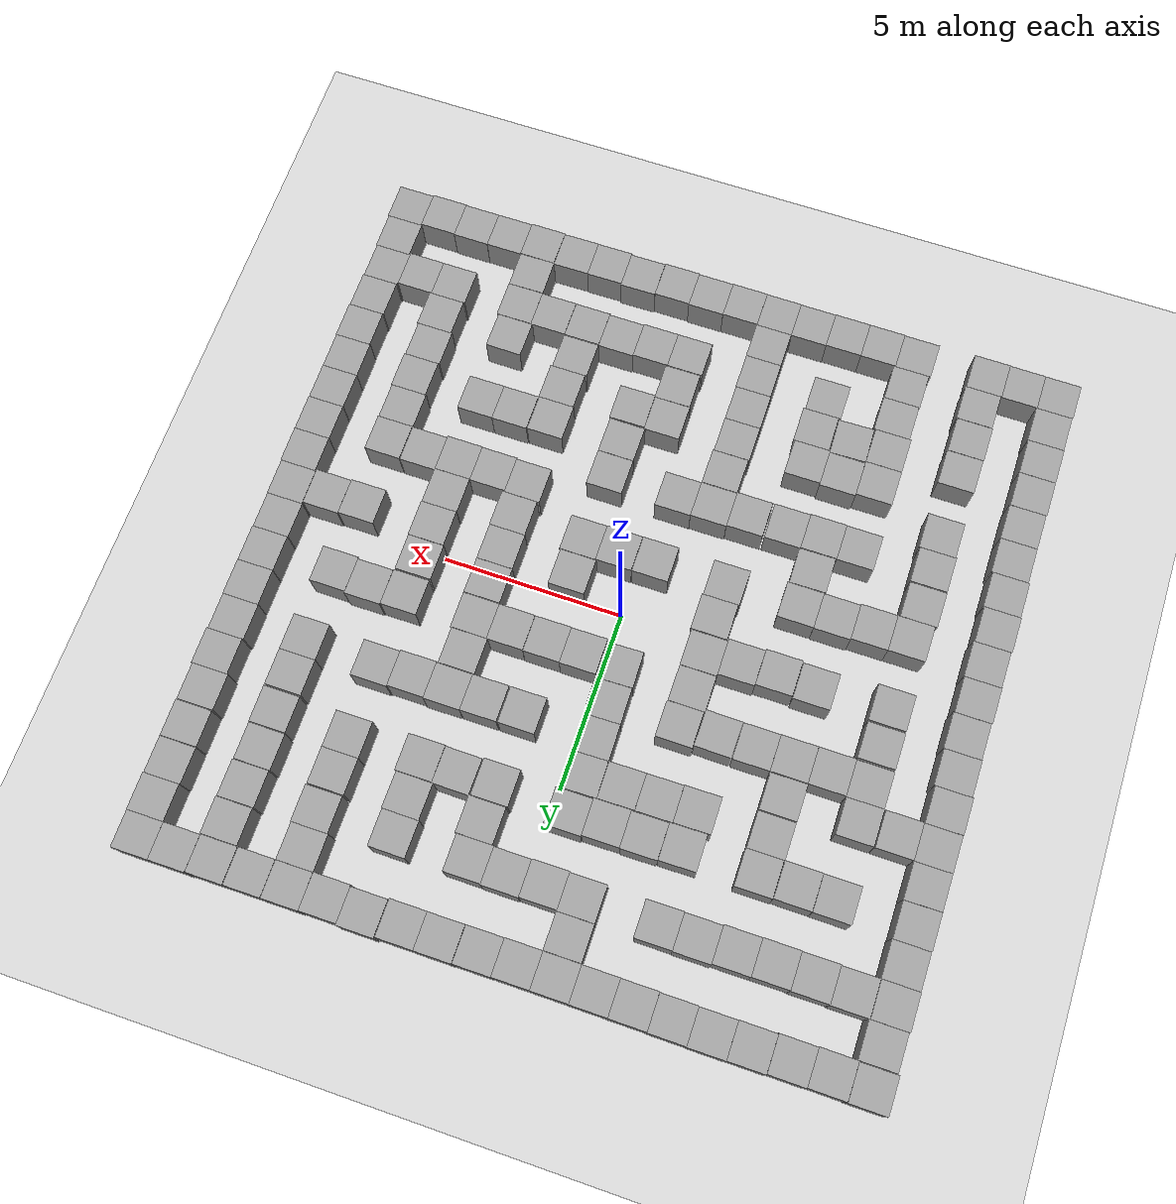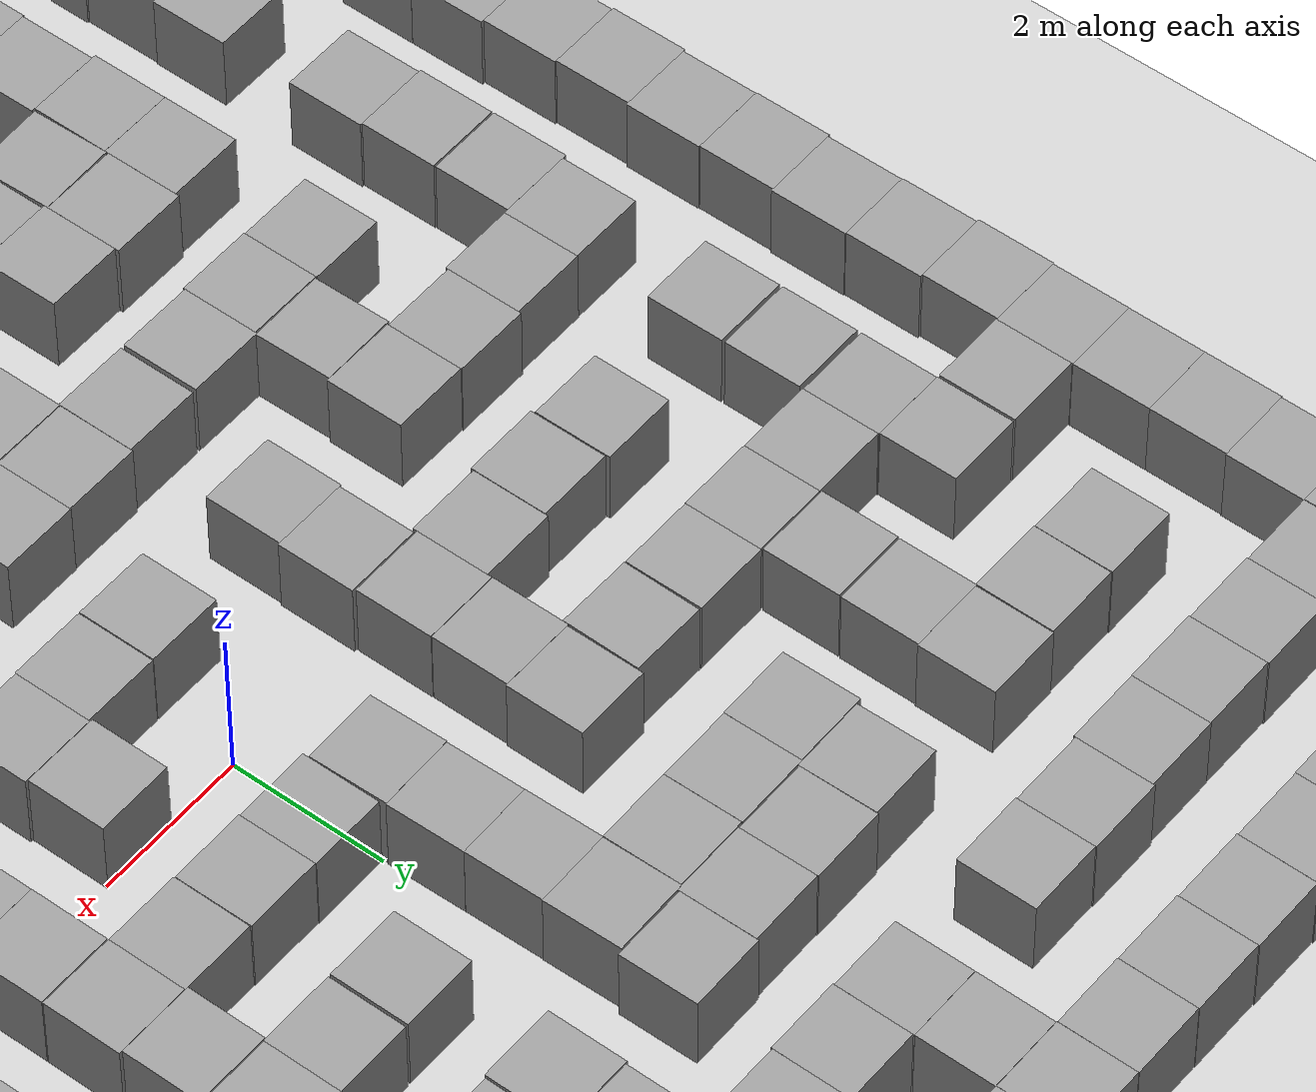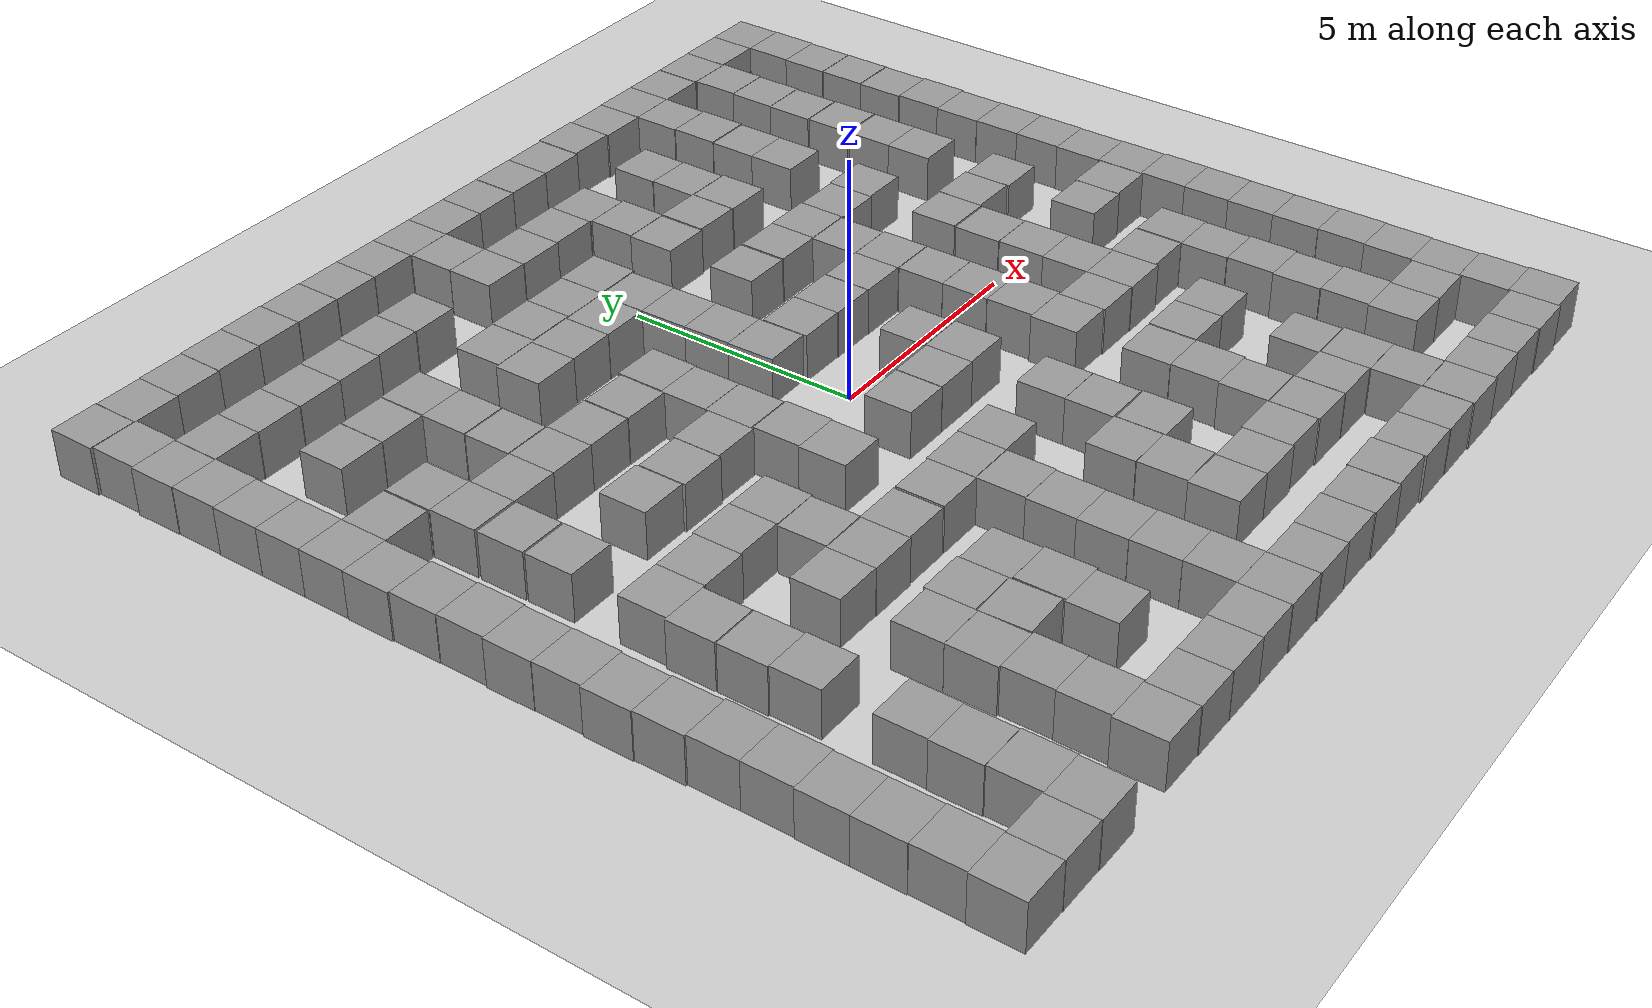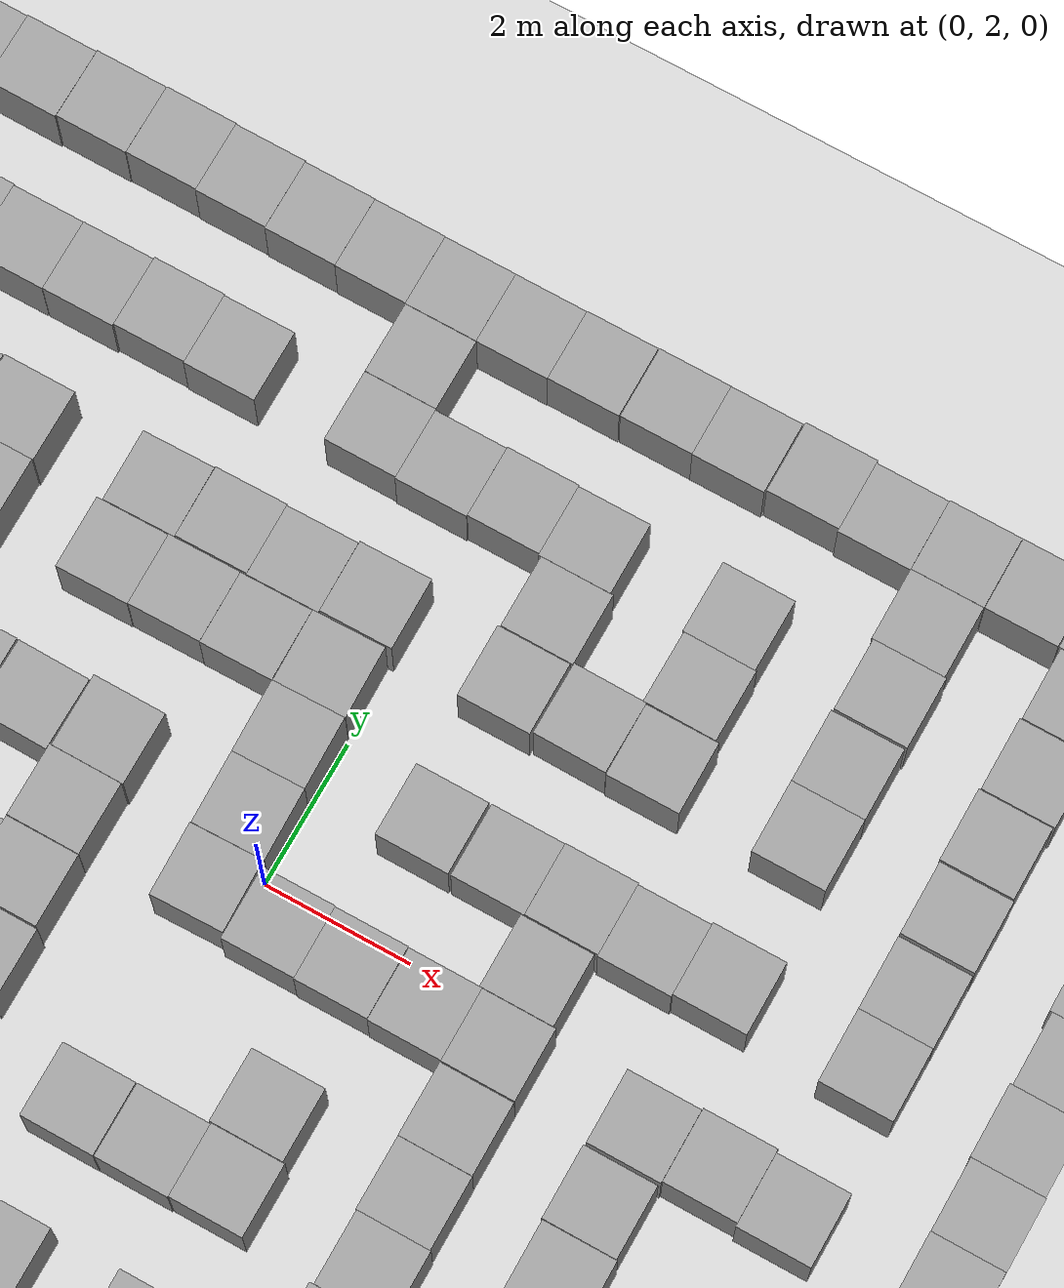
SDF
<sdf version="1.7">
 <world name="default">
  <model name="ground_plane">
   <static>1</static>
   <link name="link">
    <collision name="collision">
     <geometry><plane><normal>0 0 1</normal><size>100 100</size></plane></geometry>
     <surface><friction><ode><mu>100</mu><mu2>50</mu2></ode></friction></surface>
    </collision>
    <visual name="visual">
     <cast_shadows>0</cast_shadows>
     <geometry><plane><normal>0 0 1</normal><size>100 100</size></plane></geometry>
     <material>
      <script><uri>file://media/materials/scripts/gazebo.material</uri><name>Gazebo/Grey</name></script>
     </material>
    </visual>
   </link>
  </model>
  <light name="sun" type="directional">
   <pose>0 0 10 0 -0 0</pose>
   <diffuse>0.8 0.8 0.8 1</diffuse>
   <specular>0.2 0.2 0.2 1</specular>
   <attenuation>
    <range>1000</range>
    <constant>0.9</constant>
    <linear>0.01</linear>
    <quadratic>0.001</quadratic>
   </attenuation>
   <direction>-0.5 0.1 -0.9</direction>
   <spot><inner_angle>0</inner_angle><outer_angle>0</outer_angle><falloff>0</falloff></spot>
  </light>
  <scene><shadows>0</shadows><ambient>0.4 0.4 0.4 1</ambient><background>0.7 0.7 0.7 1</background></scene>
  <physics type="ode">
   <real_time_update_rate>1000</real_time_update_rate>
   <max_step_size>0.001</max_step_size>
   <real_time_factor>1</real_time_factor>
   <ode>
    <solver>
     <type>quick</type>
     <iters>150</iters>
     <precon_iters>0</precon_iters>
     <sor>1.4</sor>
     <use_dynamic_moi_rescaling>1</use_dynamic_moi_rescaling>
    </solver>
    <constraints>
     <cfm>1e-05</cfm>
     <erp>0.2</erp>
     <contact_max_correcting_vel>2000</contact_max_correcting_vel>
     <contact_surface_layer>0.01</contact_surface_layer>
    </constraints>
   </ode>
  </physics>
  <gravity>0 0 -9.8</gravity>
  <magnetic_field>6e-06 2.3e-05 -4.2e-05</magnetic_field>
  <atmosphere type="adiabatic"/>
  <audio><device>default</device></audio>
  <spherical_coordinates>
   <surface_model>EARTH_WGS84</surface_model>
   <latitude_deg>0</latitude_deg>
   <longitude_deg>0</longitude_deg>
   <elevation>0</elevation>
   <heading_deg>0</heading_deg>
  </spherical_coordinates>
  <model name="unit_box">
   <pose>9.53051 9.54455 0.5 0 -0 4.5e-05</pose>
   <link name="link">
    <inertial>
     <mass>1</mass>
     <inertia>
      <ixx>0.166667</ixx>
      <ixy>0</ixy>
      <ixz>0</ixz>
      <iyy>0.166667</iyy>
      <iyz>0</iyz>
      <izz>0.166667</izz>
     </inertia>
    </inertial>
    <collision name="collision"><geometry><box><size>1 1 1</size></box></geometry></collision>
    <visual name="visual">
     <geometry><box><size>1 1 1</size></box></geometry>
     <material>
      <script><name>Gazebo/Grey</name><uri>file://media/materials/scripts/gazebo.material</uri></script>
     </material>
    </visual>
   </link>
  </model>
  <model name="unit_box_0">
   <pose>8.5305 9.54105 0.5 0 -0 3.1e-05</pose>
   <link name="link">
    <inertial>
     <mass>1</mass>
     <inertia>
      <ixx>0.166667</ixx>
      <ixy>0</ixy>
      <ixz>0</ixz>
      <iyy>0.166667</iyy>
      <iyz>0</iyz>
      <izz>0.166667</izz>
     </inertia>
    </inertial>
    <collision name="collision"><geometry><box><size>1 1 1</size></box></geometry></collision>
    <visual name="visual">
     <geometry><box><size>1 1 1</size></box></geometry>
     <material>
      <script><name>Gazebo/Grey</name><uri>file://media/materials/scripts/gazebo.material</uri></script>
     </material>
    </visual>
   </link>
  </model>
  <model name="unit_box_1">
   <pose>7.52834 9.52677 0.5 0 -0 0</pose>
   <link name="link">
    <inertial>
     <mass>1</mass>
     <inertia>
      <ixx>0.166667</ixx>
      <ixy>0</ixy>
      <ixz>0</ixz>
      <iyy>0.166667</iyy>
      <iyz>0</iyz>
      <izz>0.166667</izz>
     </inertia>
    </inertial>
    <collision name="collision"><geometry><box><size>1 1 1</size></box></geometry></collision>
    <visual name="visual">
     <geometry><box><size>1 1 1</size></box></geometry>
     <material>
      <script><name>Gazebo/Grey</name><uri>file://media/materials/scripts/gazebo.material</uri></script>
     </material>
    </visual>
   </link>
  </model>
  <model name="unit_box_2">
   <pose>5.51039 9.52199 0.5 0 0 -0.000132</pose>
   <link name="link">
    <inertial>
     <mass>1</mass>
     <inertia>
      <ixx>0.166667</ixx>
      <ixy>0</ixy>
      <ixz>0</ixz>
      <iyy>0.166667</iyy>
      <iyz>0</iyz>
      <izz>0.166667</izz>
     </inertia>
    </inertial>
    <collision name="collision"><geometry><box><size>1 1 1</size></box></geometry></collision>
    <visual name="visual">
     <geometry><box><size>1 1 1</size></box></geometry>
     <material>
      <script><name>Gazebo/Grey</name><uri>file://media/materials/scripts/gazebo.material</uri></script>
     </material>
    </visual>
   </link>
  </model>
  <model name="unit_box_3">
   <pose>9.54045 8.54454 0.5 0 -0 5.8e-05</pose>
   <link name="link">
    <inertial>
     <mass>1</mass>
     <inertia>
      <ixx>0.166667</ixx>
      <ixy>0</ixy>
      <ixz>0</ixz>
      <iyy>0.166667</iyy>
      <iyz>0</iyz>
      <izz>0.166667</izz>
     </inertia>
    </inertial>
    <collision name="collision"><geometry><box><size>1 1 1</size></box></geometry></collision>
    <visual name="visual">
     <geometry><box><size>1 1 1</size></box></geometry>
     <material>
      <script><name>Gazebo/Grey</name><uri>file://media/materials/scripts/gazebo.material</uri></script>
     </material>
    </visual>
   </link>
  </model>
  <model name="unit_box_4">
   <pose>9.51774 7.54453 0.5 0 -0 4e-05</pose>
   <link name="link">
    <inertial>
     <mass>1</mass>
     <inertia>
      <ixx>0.166667</ixx>
      <ixy>0</ixy>
      <ixz>0</ixz>
      <iyy>0.166667</iyy>
      <iyz>0</iyz>
      <izz>0.166667</izz>
     </inertia>
    </inertial>
    <collision name="collision"><geometry><box><size>1 1 1</size></box></geometry></collision>
    <visual name="visual">
     <geometry><box><size>1 1 1</size></box></geometry>
     <material>
      <script><name>Gazebo/Grey</name><uri>file://media/materials/scripts/gazebo.material</uri></script>
     </material>
    </visual>
   </link>
  </model>
  <model name="unit_box_5">
   <pose>9.51835 6.53227 0.5 0 -0 0</pose>
   <link name="link">
    <inertial>
     <mass>1</mass>
     <inertia>
      <ixx>0.166667</ixx>
      <ixy>0</ixy>
      <ixz>0</ixz>
      <iyy>0.166667</iyy>
      <iyz>0</iyz>
      <izz>0.166667</izz>
     </inertia>
    </inertial>
    <collision name="collision"><geometry><box><size>1 1 1</size></box></geometry></collision>
    <visual name="visual">
     <geometry><box><size>1 1 1</size></box></geometry>
     <material>
      <script><name>Gazebo/Grey</name><uri>file://media/materials/scripts/gazebo.material</uri></script>
     </material>
    </visual>
   </link>
  </model>
  <model name="unit_box_6">
   <pose>5.50726 8.52121 0.5 0 0 -0.001691</pose>
   <link name="link">
    <inertial>
     <mass>1</mass>
     <inertia>
      <ixx>0.166667</ixx>
      <ixy>0</ixy>
      <ixz>0</ixz>
      <iyy>0.166667</iyy>
      <iyz>0</iyz>
      <izz>0.166667</izz>
     </inertia>
    </inertial>
    <collision name="collision"><geometry><box><size>1 1 1</size></box></geometry></collision>
    <visual name="visual">
     <geometry><box><size>1 1 1</size></box></geometry>
     <material>
      <script><name>Gazebo/Grey</name><uri>file://media/materials/scripts/gazebo.material</uri></script>
     </material>
    </visual>
   </link>
  </model>
  <model name="unit_box_7">
   <pose>7.55389 8.51857 0.5 0 -0 0</pose>
   <link name="link">
    <inertial>
     <mass>1</mass>
     <inertia>
      <ixx>0.166667</ixx>
      <ixy>0</ixy>
      <ixz>0</ixz>
      <iyy>0.166667</iyy>
      <iyz>0</iyz>
      <izz>0.166667</izz>
     </inertia>
    </inertial>
    <collision name="collision"><geometry><box><size>1 1 1</size></box></geometry></collision>
    <visual name="visual">
     <geometry><box><size>1 1 1</size></box></geometry>
     <material>
      <script><name>Gazebo/Grey</name><uri>file://media/materials/scripts/gazebo.material</uri></script>
     </material>
    </visual>
   </link>
  </model>
  <model name="unit_box_8">
   <pose>6.51642 9.52235 0.5 0 -0 0</pose>
   <link name="link">
    <inertial>
     <mass>1</mass>
     <inertia>
      <ixx>0.166667</ixx>
      <ixy>0</ixy>
      <ixz>0</ixz>
      <iyy>0.166667</iyy>
      <iyz>0</iyz>
      <izz>0.166667</izz>
     </inertia>
    </inertial>
    <collision name="collision"><geometry><box><size>1 1 1</size></box></geometry></collision>
    <visual name="visual">
     <geometry><box><size>1 1 1</size></box></geometry>
     <material>
      <script><name>Gazebo/Grey</name><uri>file://media/materials/scripts/gazebo.material</uri></script>
     </material>
    </visual>
   </link>
  </model>
  <model name="unit_box_9">
   <pose>7.53128 7.50762 0.5 0 -0 0</pose>
   <link name="link">
    <inertial>
     <mass>1</mass>
     <inertia>
      <ixx>0.166667</ixx>
      <ixy>0</ixy>
      <ixz>0</ixz>
      <iyy>0.166667</iyy>
      <iyz>0</iyz>
      <izz>0.166667</izz>
     </inertia>
    </inertial>
    <collision name="collision"><geometry><box><size>1 1 1</size></box></geometry></collision>
    <visual name="visual">
     <geometry><box><size>1 1 1</size></box></geometry>
     <material>
      <script><name>Gazebo/Grey</name><uri>file://media/materials/scripts/gazebo.material</uri></script>
     </material>
    </visual>
   </link>
  </model>
  <model name="unit_box_10">
   <pose>7.50856 6.49657 0.5 0 -0 0</pose>
   <link name="link">
    <inertial>
     <mass>1</mass>
     <inertia>
      <ixx>0.166667</ixx>
      <ixy>0</ixy>
      <ixz>0</ixz>
      <iyy>0.166667</iyy>
      <iyz>0</iyz>
      <izz>0.166667</izz>
     </inertia>
    </inertial>
    <collision name="collision"><geometry><box><size>1 1 1</size></box></geometry></collision>
    <visual name="visual">
     <geometry><box><size>1 1 1</size></box></geometry>
     <material>
      <script><name>Gazebo/Grey</name><uri>file://media/materials/scripts/gazebo.material</uri></script>
     </material>
    </visual>
   </link>
  </model>
  <model name="unit_box_11">
   <pose>5.52886 7.52111 0.5 0 0 -0.001804</pose>
   <link name="link">
    <inertial>
     <mass>1</mass>
     <inertia>
      <ixx>0.166667</ixx>
      <ixy>0</ixy>
      <ixz>0</ixz>
      <iyy>0.166667</iyy>
      <iyz>0</iyz>
      <izz>0.166667</izz>
     </inertia>
    </inertial>
    <collision name="collision"><geometry><box><size>1 1 1</size></box></geometry></collision>
    <visual name="visual">
     <geometry><box><size>1 1 1</size></box></geometry>
     <material>
      <script><name>Gazebo/Grey</name><uri>file://media/materials/scripts/gazebo.material</uri></script>
     </material>
    </visual>
   </link>
  </model>
  <model name="unit_box_12">
   <pose>4.50925 9.50784 0.5 -0 -0 -0.002381</pose>
   <link name="link">
    <inertial>
     <mass>1</mass>
     <inertia>
      <ixx>0.166667</ixx>
      <ixy>0</ixy>
      <ixz>0</ixz>
      <iyy>0.166667</iyy>
      <iyz>0</iyz>
      <izz>0.166667</izz>
     </inertia>
    </inertial>
    <collision name="collision"><geometry><box><size>1 1 1</size></box></geometry></collision>
    <visual name="visual">
     <geometry><box><size>1 1 1</size></box></geometry>
     <material>
      <script><name>Gazebo/Grey</name><uri>file://media/materials/scripts/gazebo.material</uri></script>
     </material>
    </visual>
   </link>
  </model>
  <model name="unit_box_13">
   <pose>5.50623 5.49299 0.5 0 0 -1.9e-05</pose>
   <link name="link">
    <inertial>
     <mass>1</mass>
     <inertia>
      <ixx>0.166667</ixx>
      <ixy>0</ixy>
      <ixz>0</ixz>
      <iyy>0.166667</iyy>
      <iyz>0</iyz>
      <izz>0.166667</izz>
     </inertia>
    </inertial>
    <collision name="collision"><geometry><box><size>1 1 1</size></box></geometry></collision>
    <visual name="visual">
     <geometry><box><size>1 1 1</size></box></geometry>
     <material>
      <script><name>Gazebo/Grey</name><uri>file://media/materials/scripts/gazebo.material</uri></script>
     </material>
    </visual>
   </link>
  </model>
  <model name="unit_box_14">
   <pose>3.4812 7.48549 0.5 0 0 -0.010022</pose>
   <link name="link">
    <inertial>
     <mass>1</mass>
     <inertia>
      <ixx>0.166667</ixx>
      <ixy>0</ixy>
      <ixz>0</ixz>
      <iyy>0.166667</iyy>
      <iyz>0</iyz>
      <izz>0.166667</izz>
     </inertia>
    </inertial>
    <collision name="collision"><geometry><box><size>1 1 1</size></box></geometry></collision>
    <visual name="visual">
     <geometry><box><size>1 1 1</size></box></geometry>
     <material>
      <script><name>Gazebo/Grey</name><uri>file://media/materials/scripts/gazebo.material</uri></script>
     </material>
    </visual>
   </link>
  </model>
  <model name="unit_box_15">
   <pose>3.48987 6.48531 0.5 0 0 -0.010022</pose>
   <link name="link">
    <inertial>
     <mass>1</mass>
     <inertia>
      <ixx>0.166667</ixx>
      <ixy>0</ixy>
      <ixz>0</ixz>
      <iyy>0.166667</iyy>
      <iyz>0</iyz>
      <izz>0.166667</izz>
     </inertia>
    </inertial>
    <collision name="collision"><geometry><box><size>1 1 1</size></box></geometry></collision>
    <visual name="visual">
     <geometry><box><size>1 1 1</size></box></geometry>
     <material>
      <script><name>Gazebo/Grey</name><uri>file://media/materials/scripts/gazebo.material</uri></script>
     </material>
    </visual>
   </link>
  </model>
  <model name="unit_box_16">
   <pose>3.50929 9.54496 0.5 0 0 -0.002316</pose>
   <link name="link">
    <inertial>
     <mass>1</mass>
     <inertia>
      <ixx>0.166667</ixx>
      <ixy>0</ixy>
      <ixz>0</ixz>
      <iyy>0.166667</iyy>
      <iyz>0</iyz>
      <izz>0.166667</izz>
     </inertia>
    </inertial>
    <collision name="collision"><geometry><box><size>1 1 1</size></box></geometry></collision>
    <visual name="visual">
     <geometry><box><size>1 1 1</size></box></geometry>
     <material>
      <script><name>Gazebo/Grey</name><uri>file://media/materials/scripts/gazebo.material</uri></script>
     </material>
    </visual>
   </link>
  </model>
  <model name="unit_box_17">
   <pose>5.50717 6.49299 0.5 0 0 -1.9e-05</pose>
   <link name="link">
    <inertial>
     <mass>1</mass>
     <inertia>
      <ixx>0.166667</ixx>
      <ixy>0</ixy>
      <ixz>0</ixz>
      <iyy>0.166667</iyy>
      <iyz>0</iyz>
      <izz>0.166667</izz>
     </inertia>
    </inertial>
    <collision name="collision"><geometry><box><size>1 1 1</size></box></geometry></collision>
    <visual name="visual">
     <geometry><box><size>1 1 1</size></box></geometry>
     <material>
      <script><name>Gazebo/Grey</name><uri>file://media/materials/scripts/gazebo.material</uri></script>
     </material>
    </visual>
   </link>
  </model>
  <model name="unit_box_18">
   <pose>3.53377 5.47451 0.5 0 -0 0.000896</pose>
   <link name="link">
    <inertial>
     <mass>1</mass>
     <inertia>
      <ixx>0.166667</ixx>
      <ixy>0</ixy>
      <ixz>0</ixz>
      <iyy>0.166667</iyy>
      <iyz>0</iyz>
      <izz>0.166667</izz>
     </inertia>
    </inertial>
    <collision name="collision"><geometry><box><size>1 1 1</size></box></geometry></collision>
    <visual name="visual">
     <geometry><box><size>1 1 1</size></box></geometry>
     <material>
      <script><name>Gazebo/Grey</name><uri>file://media/materials/scripts/gazebo.material</uri></script>
     </material>
    </visual>
   </link>
  </model>
  <model name="unit_box_19">
   <pose>2.52803 5.49531 0.5 0 0 -0.010949</pose>
   <link name="link">
    <inertial>
     <mass>1</mass>
     <inertia>
      <ixx>0.166667</ixx>
      <ixy>0</ixy>
      <ixz>0</ixz>
      <iyy>0.166667</iyy>
      <iyz>0</iyz>
      <izz>0.166667</izz>
     </inertia>
    </inertial>
    <collision name="collision"><geometry><box><size>1 1 1</size></box></geometry></collision>
    <visual name="visual">
     <geometry><box><size>1 1 1</size></box></geometry>
     <material>
      <script><name>Gazebo/Grey</name><uri>file://media/materials/scripts/gazebo.material</uri></script>
     </material>
    </visual>
   </link>
  </model>
  <model name="unit_box_20">
   <pose>1.49725 5.46583 0.5 0 -0 0</pose>
   <link name="link">
    <inertial>
     <mass>1</mass>
     <inertia>
      <ixx>0.166667</ixx>
      <ixy>0</ixy>
      <ixz>0</ixz>
      <iyy>0.166667</iyy>
      <iyz>0</iyz>
      <izz>0.166667</izz>
     </inertia>
    </inertial>
    <collision name="collision"><geometry><box><size>1 1 1</size></box></geometry></collision>
    <visual name="visual">
     <geometry><box><size>1 1 1</size></box></geometry>
     <material>
      <script><name>Gazebo/Grey</name><uri>file://media/materials/scripts/gazebo.material</uri></script>
     </material>
    </visual>
   </link>
  </model>
  <model name="unit_box_21">
   <pose>1.53008 6.47633 0.5 0 0 -0.001949</pose>
   <link name="link">
    <inertial>
     <mass>1</mass>
     <inertia>
      <ixx>0.166667</ixx>
      <ixy>0</ixy>
      <ixz>0</ixz>
      <iyy>0.166667</iyy>
      <iyz>0</iyz>
      <izz>0.166667</izz>
     </inertia>
    </inertial>
    <collision name="collision"><geometry><box><size>1 1 1</size></box></geometry></collision>
    <visual name="visual">
     <geometry><box><size>1 1 1</size></box></geometry>
     <material>
      <script><name>Gazebo/Grey</name><uri>file://media/materials/scripts/gazebo.material</uri></script>
     </material>
    </visual>
   </link>
  </model>
  <model name="unit_box_22">
   <pose>1.49099 7.47703 0.5 -0 -0 -0.000907</pose>
   <link name="link">
    <inertial>
     <mass>1</mass>
     <inertia>
      <ixx>0.166667</ixx>
      <ixy>0</ixy>
      <ixz>0</ixz>
      <iyy>0.166667</iyy>
      <iyz>0</iyz>
      <izz>0.166667</izz>
     </inertia>
    </inertial>
    <collision name="collision"><geometry><box><size>1 1 1</size></box></geometry></collision>
    <visual name="visual">
     <geometry><box><size>1 1 1</size></box></geometry>
     <material>
      <script><name>Gazebo/Grey</name><uri>file://media/materials/scripts/gazebo.material</uri></script>
     </material>
    </visual>
   </link>
  </model>
  <model name="unit_box_23">
   <pose>0.490998 7.49385 0.5 0 0 -0.0009</pose>
   <link name="link">
    <inertial>
     <mass>1</mass>
     <inertia>
      <ixx>0.166667</ixx>
      <ixy>0</ixy>
      <ixz>0</ixz>
      <iyy>0.166667</iyy>
      <iyz>0</iyz>
      <izz>0.166667</izz>
     </inertia>
    </inertial>
    <collision name="collision"><geometry><box><size>1 1 1</size></box></geometry></collision>
    <visual name="visual">
     <geometry><box><size>1 1 1</size></box></geometry>
     <material>
      <script><name>Gazebo/Grey</name><uri>file://media/materials/scripts/gazebo.material</uri></script>
     </material>
    </visual>
   </link>
  </model>
  <model name="unit_box_24">
   <pose>-0.509041 7.47722 0.5 -0 -0 -0.00085</pose>
   <link name="link">
    <inertial>
     <mass>1</mass>
     <inertia>
      <ixx>0.166667</ixx>
      <ixy>0</ixy>
      <ixz>0</ixz>
      <iyy>0.166667</iyy>
      <iyz>0</iyz>
      <izz>0.166667</izz>
     </inertia>
    </inertial>
    <collision name="collision"><geometry><box><size>1 1 1</size></box></geometry></collision>
    <visual name="visual">
     <geometry><box><size>1 1 1</size></box></geometry>
     <material>
      <script><name>Gazebo/Grey</name><uri>file://media/materials/scripts/gazebo.material</uri></script>
     </material>
    </visual>
   </link>
  </model>
  <model name="unit_box_25">
   <pose>2.49454 9.50871 0.5 -0 -0 -1.8e-05</pose>
   <link name="link">
    <inertial>
     <mass>1</mass>
     <inertia>
      <ixx>0.166667</ixx>
      <ixy>0</ixy>
      <ixz>0</ixz>
      <iyy>0.166667</iyy>
      <iyz>0</iyz>
      <izz>0.166667</izz>
     </inertia>
    </inertial>
    <collision name="collision"><geometry><box><size>1 1 1</size></box></geometry></collision>
    <visual name="visual">
     <geometry><box><size>1 1 1</size></box></geometry>
     <material>
      <script><name>Gazebo/Grey</name><uri>file://media/materials/scripts/gazebo.material</uri></script>
     </material>
    </visual>
   </link>
  </model>
  <model name="unit_box_26">
   <pose>1.49454 9.51183 0.5 0 0 -1.7e-05</pose>
   <link name="link">
    <inertial>
     <mass>1</mass>
     <inertia>
      <ixx>0.166667</ixx>
      <ixy>0</ixy>
      <ixz>0</ixz>
      <iyy>0.166667</iyy>
      <iyz>0</iyz>
      <izz>0.166667</izz>
     </inertia>
    </inertial>
    <collision name="collision"><geometry><box><size>1 1 1</size></box></geometry></collision>
    <visual name="visual">
     <geometry><box><size>1 1 1</size></box></geometry>
     <material>
      <script><name>Gazebo/Grey</name><uri>file://media/materials/scripts/gazebo.material</uri></script>
     </material>
    </visual>
   </link>
  </model>
  <model name="unit_box_27">
   <pose>0.483935 9.50421 0.5 -0 -0 -0.000607</pose>
   <link name="link">
    <inertial>
     <mass>1</mass>
     <inertia>
      <ixx>0.166667</ixx>
      <ixy>0</ixy>
      <ixz>0</ixz>
      <iyy>0.166667</iyy>
      <iyz>0</iyz>
      <izz>0.166667</izz>
     </inertia>
    </inertial>
    <collision name="collision"><geometry><box><size>1 1 1</size></box></geometry></collision>
    <visual name="visual">
     <geometry><box><size>1 1 1</size></box></geometry>
     <material>
      <script><name>Gazebo/Grey</name><uri>file://media/materials/scripts/gazebo.material</uri></script>
     </material>
    </visual>
   </link>
  </model>
  <model name="unit_box_28">
   <pose>-0.516085 9.49636 0.5 -0 -0 -0.000638</pose>
   <link name="link">
    <inertial>
     <mass>1</mass>
     <inertia>
      <ixx>0.166667</ixx>
      <ixy>0</ixy>
      <ixz>0</ixz>
      <iyy>0.166667</iyy>
      <iyz>0</iyz>
      <izz>0.166667</izz>
     </inertia>
    </inertial>
    <collision name="collision"><geometry><box><size>1 1 1</size></box></geometry></collision>
    <visual name="visual">
     <geometry><box><size>1 1 1</size></box></geometry>
     <material>
      <script><name>Gazebo/Grey</name><uri>file://media/materials/scripts/gazebo.material</uri></script>
     </material>
    </visual>
   </link>
  </model>
  <model name="unit_box_29">
   <pose>-1.51618 9.49897 0.5 0 0 -0.000832</pose>
   <link name="link">
    <inertial>
     <mass>1</mass>
     <inertia>
      <ixx>0.166667</ixx>
      <ixy>0</ixy>
      <ixz>0</ixz>
      <iyy>0.166667</iyy>
      <iyz>0</iyz>
      <izz>0.166667</izz>
     </inertia>
    </inertial>
    <collision name="collision"><geometry><box><size>1 1 1</size></box></geometry></collision>
    <visual name="visual">
     <geometry><box><size>1 1 1</size></box></geometry>
     <material>
      <script><name>Gazebo/Grey</name><uri>file://media/materials/scripts/gazebo.material</uri></script>
     </material>
    </visual>
   </link>
  </model>
  <model name="unit_box_30">
   <pose>-1.50811 8.49539 0.5 -0 -0 -0.002751</pose>
   <link name="link">
    <inertial>
     <mass>1</mass>
     <inertia>
      <ixx>0.166667</ixx>
      <ixy>0</ixy>
      <ixz>0</ixz>
      <iyy>0.166667</iyy>
      <iyz>0</iyz>
      <izz>0.166667</izz>
     </inertia>
    </inertial>
    <collision name="collision"><geometry><box><size>1 1 1</size></box></geometry></collision>
    <visual name="visual">
     <geometry><box><size>1 1 1</size></box></geometry>
     <material>
      <script><name>Gazebo/Grey</name><uri>file://media/materials/scripts/gazebo.material</uri></script>
     </material>
    </visual>
   </link>
  </model>
  <model name="unit_box_31">
   <pose>-1.50908 7.49382 0.5 0 0 -0.000782</pose>
   <link name="link">
    <inertial>
     <mass>1</mass>
     <inertia>
      <ixx>0.166667</ixx>
      <ixy>0</ixy>
      <ixz>0</ixz>
      <iyy>0.166667</iyy>
      <iyz>0</iyz>
      <izz>0.166667</izz>
     </inertia>
    </inertial>
    <collision name="collision"><geometry><box><size>1 1 1</size></box></geometry></collision>
    <visual name="visual">
     <geometry><box><size>1 1 1</size></box></geometry>
     <material>
      <script><name>Gazebo/Grey</name><uri>file://media/materials/scripts/gazebo.material</uri></script>
     </material>
    </visual>
   </link>
  </model>
  <model name="unit_box_32">
   <pose>5.52577 3.50952 0.5 0 0 -5.5e-05</pose>
   <link name="link">
    <inertial>
     <mass>1</mass>
     <inertia>
      <ixx>0.166667</ixx>
      <ixy>0</ixy>
      <ixz>0</ixz>
      <iyy>0.166667</iyy>
      <iyz>0</iyz>
      <izz>0.166667</izz>
     </inertia>
    </inertial>
    <collision name="collision"><geometry><box><size>1 1 1</size></box></geometry></collision>
    <visual name="visual">
     <geometry><box><size>1 1 1</size></box></geometry>
     <material>
      <script><name>Gazebo/Grey</name><uri>file://media/materials/scripts/gazebo.material</uri></script>
     </material>
    </visual>
   </link>
  </model>
  <model name="unit_box_33">
   <pose>4.52576 3.47865 0.5 0 0 -5.5e-05</pose>
   <link name="link">
    <inertial>
     <mass>1</mass>
     <inertia>
      <ixx>0.166667</ixx>
      <ixy>0</ixy>
      <ixz>0</ixz>
      <iyy>0.166667</iyy>
      <iyz>0</iyz>
      <izz>0.166667</izz>
     </inertia>
    </inertial>
    <collision name="collision"><geometry><box><size>1 1 1</size></box></geometry></collision>
    <visual name="visual">
     <geometry><box><size>1 1 1</size></box></geometry>
     <material>
      <script><name>Gazebo/Grey</name><uri>file://media/materials/scripts/gazebo.material</uri></script>
     </material>
    </visual>
   </link>
  </model>
  <model name="unit_box_34">
   <pose>3.52573 3.49888 0.5 0 0 -5.7e-05</pose>
   <link name="link">
    <inertial>
     <mass>1</mass>
     <inertia>
      <ixx>0.166667</ixx>
      <ixy>0</ixy>
      <ixz>0</ixz>
      <iyy>0.166667</iyy>
      <iyz>0</iyz>
      <izz>0.166667</izz>
     </inertia>
    </inertial>
    <collision name="collision"><geometry><box><size>1 1 1</size></box></geometry></collision>
    <visual name="visual">
     <geometry><box><size>1 1 1</size></box></geometry>
     <material>
      <script><name>Gazebo/Grey</name><uri>file://media/materials/scripts/gazebo.material</uri></script>
     </material>
    </visual>
   </link>
  </model>
  <model name="unit_box_35">
   <pose>2.52569 3.49064 0.5 0 0 -5.7e-05</pose>
   <link name="link">
    <inertial>
     <mass>1</mass>
     <inertia>
      <ixx>0.166667</ixx>
      <ixy>0</ixy>
      <ixz>0</ixz>
      <iyy>0.166667</iyy>
      <iyz>0</iyz>
      <izz>0.166667</izz>
     </inertia>
    </inertial>
    <collision name="collision"><geometry><box><size>1 1 1</size></box></geometry></collision>
    <visual name="visual">
     <geometry><box><size>1 1 1</size></box></geometry>
     <material>
      <script><name>Gazebo/Grey</name><uri>file://media/materials/scripts/gazebo.material</uri></script>
     </material>
    </visual>
   </link>
  </model>
  <model name="unit_box_36">
   <pose>1.49223 3.48855 0.5 0 -0 0</pose>
   <link name="link">
    <inertial>
     <mass>1</mass>
     <inertia>
      <ixx>0.166667</ixx>
      <ixy>0</ixy>
      <ixz>0</ixz>
      <iyy>0.166667</iyy>
      <iyz>0</iyz>
      <izz>0.166667</izz>
     </inertia>
    </inertial>
    <collision name="collision"><geometry><box><size>1 1 1</size></box></geometry></collision>
    <visual name="visual">
     <geometry><box><size>1 1 1</size></box></geometry>
     <material>
      <script><name>Gazebo/Grey</name><uri>file://media/materials/scripts/gazebo.material</uri></script>
     </material>
    </visual>
   </link>
  </model>
  <model name="unit_box_37">
   <pose>3.48857 2.48305 0.5 0 -0 -0.000498</pose>
   <link name="link">
    <inertial>
     <mass>1</mass>
     <inertia>
      <ixx>0.166667</ixx>
      <ixy>0</ixy>
      <ixz>0</ixz>
      <iyy>0.166667</iyy>
      <iyz>0</iyz>
      <izz>0.166667</izz>
     </inertia>
    </inertial>
    <collision name="collision"><geometry><box><size>1 1 1</size></box></geometry></collision>
    <visual name="visual">
     <geometry><box><size>1 1 1</size></box></geometry>
     <material>
      <script><name>Gazebo/Grey</name><uri>file://media/materials/scripts/gazebo.material</uri></script>
     </material>
    </visual>
   </link>
  </model>
  <model name="unit_box_38">
   <pose>3.52867 1.4796 0.5 0 0 -6.3e-05</pose>
   <link name="link">
    <inertial>
     <mass>1</mass>
     <inertia>
      <ixx>0.166667</ixx>
      <ixy>0</ixy>
      <ixz>0</ixz>
      <iyy>0.166667</iyy>
      <iyz>0</iyz>
      <izz>0.166667</izz>
     </inertia>
    </inertial>
    <collision name="collision"><geometry><box><size>1 1 1</size></box></geometry></collision>
    <visual name="visual">
     <geometry><box><size>1 1 1</size></box></geometry>
     <material>
      <script><name>Gazebo/Grey</name><uri>file://media/materials/scripts/gazebo.material</uri></script>
     </material>
    </visual>
   </link>
  </model>
  <model name="unit_box_39">
   <pose>2.52867 1.48331 0.5 0 -0 -6.4e-05</pose>
   <link name="link">
    <inertial>
     <mass>1</mass>
     <inertia>
      <ixx>0.166667</ixx>
      <ixy>0</ixy>
      <ixz>0</ixz>
      <iyy>0.166667</iyy>
      <iyz>0</iyz>
      <izz>0.166667</izz>
     </inertia>
    </inertial>
    <collision name="collision"><geometry><box><size>1 1 1</size></box></geometry></collision>
    <visual name="visual">
     <geometry><box><size>1 1 1</size></box></geometry>
     <material>
      <script><name>Gazebo/Grey</name><uri>file://media/materials/scripts/gazebo.material</uri></script>
     </material>
    </visual>
   </link>
  </model>
  <model name="unit_box_40">
   <pose>1.52252 1.49038 0.5 0 -0 0.005113</pose>
   <link name="link">
    <inertial>
     <mass>1</mass>
     <inertia>
      <ixx>0.166667</ixx>
      <ixy>0</ixy>
      <ixz>0</ixz>
      <iyy>0.166667</iyy>
      <iyz>0</iyz>
      <izz>0.166667</izz>
     </inertia>
    </inertial>
    <collision name="collision"><geometry><box><size>1 1 1</size></box></geometry></collision>
    <visual name="visual">
     <geometry><box><size>1 1 1</size></box></geometry>
     <material>
      <script><name>Gazebo/Grey</name><uri>file://media/materials/scripts/gazebo.material</uri></script>
     </material>
    </visual>
   </link>
  </model>
  <model name="unit_box_41">
   <pose>0.522453 1.49557 0.5 0 -0 0.005069</pose>
   <link name="link">
    <inertial>
     <mass>1</mass>
     <inertia>
      <ixx>0.166667</ixx>
      <ixy>0</ixy>
      <ixz>0</ixz>
      <iyy>0.166667</iyy>
      <iyz>0</iyz>
      <izz>0.166667</izz>
     </inertia>
    </inertial>
    <collision name="collision"><geometry><box><size>1 1 1</size></box></geometry></collision>
    <visual name="visual">
     <geometry><box><size>1 1 1</size></box></geometry>
     <material>
      <script><name>Gazebo/Grey</name><uri>file://media/materials/scripts/gazebo.material</uri></script>
     </material>
    </visual>
   </link>
  </model>
  <model name="unit_box_42">
   <pose>-0.49519 1.55293 0.5 0 -0 0.022818</pose>
   <link name="link">
    <inertial>
     <mass>1</mass>
     <inertia>
      <ixx>0.166667</ixx>
      <ixy>0</ixy>
      <ixz>0</ixz>
      <iyy>0.166667</iyy>
      <iyz>0</iyz>
      <izz>0.166667</izz>
     </inertia>
    </inertial>
    <collision name="collision"><geometry><box><size>1 1 1</size></box></geometry></collision>
    <visual name="visual">
     <geometry><box><size>1 1 1</size></box></geometry>
     <material>
      <script><name>Gazebo/Grey</name><uri>file://media/materials/scripts/gazebo.material</uri></script>
     </material>
    </visual>
   </link>
  </model>
  <model name="unit_box_43">
   <pose>-0.504213 2.55469 0.5 0 -0 0.019391</pose>
   <link name="link">
    <inertial>
     <mass>1</mass>
     <inertia>
      <ixx>0.166667</ixx>
      <ixy>0</ixy>
      <ixz>0</ixz>
      <iyy>0.166667</iyy>
      <iyz>0</iyz>
      <izz>0.166667</izz>
     </inertia>
    </inertial>
    <collision name="collision"><geometry><box><size>1 1 1</size></box></geometry></collision>
    <visual name="visual">
     <geometry><box><size>1 1 1</size></box></geometry>
     <material>
      <script><name>Gazebo/Grey</name><uri>file://media/materials/scripts/gazebo.material</uri></script>
     </material>
    </visual>
   </link>
  </model>
  <model name="unit_box_44">
   <pose>-0.525074 3.55463 0.5 0 -0 0.01907</pose>
   <link name="link">
    <inertial>
     <mass>1</mass>
     <inertia>
      <ixx>0.166667</ixx>
      <ixy>0</ixy>
      <ixz>0</ixz>
      <iyy>0.166667</iyy>
      <iyz>0</iyz>
      <izz>0.166667</izz>
     </inertia>
    </inertial>
    <collision name="collision"><geometry><box><size>1 1 1</size></box></geometry></collision>
    <visual name="visual">
     <geometry><box><size>1 1 1</size></box></geometry>
     <material>
      <script><name>Gazebo/Grey</name><uri>file://media/materials/scripts/gazebo.material</uri></script>
     </material>
    </visual>
   </link>
  </model>
  <model name="unit_box_45">
   <pose>-0.537463 4.55458 0.5 0 -0 0.019058</pose>
   <link name="link">
    <inertial>
     <mass>1</mass>
     <inertia>
      <ixx>0.166667</ixx>
      <ixy>0</ixy>
      <ixz>0</ixz>
      <iyy>0.166667</iyy>
      <iyz>0</iyz>
      <izz>0.166667</izz>
     </inertia>
    </inertial>
    <collision name="collision"><geometry><box><size>1 1 1</size></box></geometry></collision>
    <visual name="visual">
     <geometry><box><size>1 1 1</size></box></geometry>
     <material>
      <script><name>Gazebo/Grey</name><uri>file://media/materials/scripts/gazebo.material</uri></script>
     </material>
    </visual>
   </link>
  </model>
  <model name="unit_box_46">
   <pose>-0.47556 5.57724 0.5 0 -0 0.006725</pose>
   <link name="link">
    <inertial>
     <mass>1</mass>
     <inertia>
      <ixx>0.166667</ixx>
      <ixy>0</ixy>
      <ixz>0</ixz>
      <iyy>0.166667</iyy>
      <iyz>0</iyz>
      <izz>0.166667</izz>
     </inertia>
    </inertial>
    <collision name="collision"><geometry><box><size>1 1 1</size></box></geometry></collision>
    <visual name="visual">
     <geometry><box><size>1 1 1</size></box></geometry>
     <material>
      <script><name>Gazebo/Grey</name><uri>file://media/materials/scripts/gazebo.material</uri></script>
     </material>
    </visual>
   </link>
  </model>
  <model name="unit_box_47">
   <pose>3.52988 0.465657 0.5 0 -0 0</pose>
   <link name="link">
    <inertial>
     <mass>1</mass>
     <inertia>
      <ixx>0.166667</ixx>
      <ixy>0</ixy>
      <ixz>0</ixz>
      <iyy>0.166667</iyy>
      <iyz>0</iyz>
      <izz>0.166667</izz>
     </inertia>
    </inertial>
    <collision name="collision"><geometry><box><size>1 1 1</size></box></geometry></collision>
    <visual name="visual">
     <geometry><box><size>1 1 1</size></box></geometry>
     <material>
      <script><name>Gazebo/Grey</name><uri>file://media/materials/scripts/gazebo.material</uri></script>
     </material>
    </visual>
   </link>
  </model>
  <model name="unit_box_48">
   <pose>7.52212 5.47616 0.5 0 -0 0</pose>
   <link name="link">
    <inertial>
     <mass>1</mass>
     <inertia>
      <ixx>0.166667</ixx>
      <ixy>0</ixy>
      <ixz>0</ixz>
      <iyy>0.166667</iyy>
      <iyz>0</iyz>
      <izz>0.166667</izz>
     </inertia>
    </inertial>
    <collision name="collision"><geometry><box><size>1 1 1</size></box></geometry></collision>
    <visual name="visual">
     <geometry><box><size>1 1 1</size></box></geometry>
     <material>
      <script><name>Gazebo/Grey</name><uri>file://media/materials/scripts/gazebo.material</uri></script>
     </material>
    </visual>
   </link>
  </model>
  <model name="unit_box_49">
   <pose>7.52036 4.43656 0.5 0 -0 5e-06</pose>
   <link name="link">
    <inertial>
     <mass>1</mass>
     <inertia>
      <ixx>0.166667</ixx>
      <ixy>0</ixy>
      <ixz>0</ixz>
      <iyy>0.166667</iyy>
      <iyz>0</iyz>
      <izz>0.166667</izz>
     </inertia>
    </inertial>
    <collision name="collision"><geometry><box><size>1 1 1</size></box></geometry></collision>
    <visual name="visual">
     <geometry><box><size>1 1 1</size></box></geometry>
     <material>
      <script><name>Gazebo/Grey</name><uri>file://media/materials/scripts/gazebo.material</uri></script>
     </material>
    </visual>
   </link>
  </model>
  <model name="unit_box_50">
   <pose>7.52026 3.43655 0.5 0 -0 0</pose>
   <link name="link">
    <inertial>
     <mass>1</mass>
     <inertia>
      <ixx>0.166667</ixx>
      <ixy>0</ixy>
      <ixz>0</ixz>
      <iyy>0.166667</iyy>
      <iyz>0</iyz>
      <izz>0.166667</izz>
     </inertia>
    </inertial>
    <collision name="collision"><geometry><box><size>1 1 1</size></box></geometry></collision>
    <visual name="visual">
     <geometry><box><size>1 1 1</size></box></geometry>
     <material>
      <script><name>Gazebo/Grey</name><uri>file://media/materials/scripts/gazebo.material</uri></script>
     </material>
    </visual>
   </link>
  </model>
  <model name="unit_box_51">
   <pose>7.50023 1.44837 0.5 0 -0 0</pose>
   <link name="link">
    <inertial>
     <mass>1</mass>
     <inertia>
      <ixx>0.166667</ixx>
      <ixy>0</ixy>
      <ixz>0</ixz>
      <iyy>0.166667</iyy>
      <iyz>0</iyz>
      <izz>0.166667</izz>
     </inertia>
    </inertial>
    <collision name="collision"><geometry><box><size>1 1 1</size></box></geometry></collision>
    <visual name="visual">
     <geometry><box><size>1 1 1</size></box></geometry>
     <material>
      <script><name>Gazebo/Grey</name><uri>file://media/materials/scripts/gazebo.material</uri></script>
     </material>
    </visual>
   </link>
  </model>
  <model name="unit_box_52">
   <pose>6.49881 1.49368 0.5 0 -0 0</pose>
   <link name="link">
    <inertial>
     <mass>1</mass>
     <inertia>
      <ixx>0.166667</ixx>
      <ixy>0</ixy>
      <ixz>0</ixz>
      <iyy>0.166667</iyy>
      <iyz>0</iyz>
      <izz>0.166667</izz>
     </inertia>
    </inertial>
    <collision name="collision"><geometry><box><size>1 1 1</size></box></geometry></collision>
    <visual name="visual">
     <geometry><box><size>1 1 1</size></box></geometry>
     <material>
      <script><name>Gazebo/Grey</name><uri>file://media/materials/scripts/gazebo.material</uri></script>
     </material>
    </visual>
   </link>
  </model>
  <model name="unit_box_53">
   <pose>5.49618 1.4669 0.5 0 -0 0</pose>
   <link name="link">
    <inertial>
     <mass>1</mass>
     <inertia>
      <ixx>0.166667</ixx>
      <ixy>0</ixy>
      <ixz>0</ixz>
      <iyy>0.166667</iyy>
      <iyz>0</iyz>
      <izz>0.166667</izz>
     </inertia>
    </inertial>
    <collision name="collision"><geometry><box><size>1 1 1</size></box></geometry></collision>
    <visual name="visual">
     <geometry><box><size>1 1 1</size></box></geometry>
     <material>
      <script><name>Gazebo/Grey</name><uri>file://media/materials/scripts/gazebo.material</uri></script>
     </material>
    </visual>
   </link>
  </model>
  <model name="unit_box_54">
   <pose>3.53321 -0.535788 0.5 0 -0 -0.000787</pose>
   <link name="link">
    <inertial>
     <mass>1</mass>
     <inertia>
      <ixx>0.166667</ixx>
      <ixy>0</ixy>
      <ixz>0</ixz>
      <iyy>0.166667</iyy>
      <iyz>0</iyz>
      <izz>0.166667</izz>
     </inertia>
    </inertial>
    <collision name="collision"><geometry><box><size>1 1 1</size></box></geometry></collision>
    <visual name="visual">
     <geometry><box><size>1 1 1</size></box></geometry>
     <material>
      <script><name>Gazebo/Grey</name><uri>file://media/materials/scripts/gazebo.material</uri></script>
     </material>
    </visual>
   </link>
  </model>
  <model name="unit_box_55">
   <pose>5.47886 0.428025 0.5 0 -0 0</pose>
   <link name="link">
    <inertial>
     <mass>1</mass>
     <inertia>
      <ixx>0.166667</ixx>
      <ixy>0</ixy>
      <ixz>0</ixz>
      <iyy>0.166667</iyy>
      <iyz>0</iyz>
      <izz>0.166667</izz>
     </inertia>
    </inertial>
    <collision name="collision"><geometry><box><size>1 1 1</size></box></geometry></collision>
    <visual name="visual">
     <geometry><box><size>1 1 1</size></box></geometry>
     <material>
      <script><name>Gazebo/Grey</name><uri>file://media/materials/scripts/gazebo.material</uri></script>
     </material>
    </visual>
   </link>
  </model>
  <model name="unit_box_56">
   <pose>5.49566 -0.577664 0.5 0 -0 0.003498</pose>
   <link name="link">
    <inertial>
     <mass>1</mass>
     <inertia>
      <ixx>0.166667</ixx>
      <ixy>0</ixy>
      <ixz>0</ixz>
      <iyy>0.166667</iyy>
      <iyz>0</iyz>
      <izz>0.166667</izz>
     </inertia>
    </inertial>
    <collision name="collision"><geometry><box><size>1 1 1</size></box></geometry></collision>
    <visual name="visual">
     <geometry><box><size>1 1 1</size></box></geometry>
     <material>
      <script><name>Gazebo/Grey</name><uri>file://media/materials/scripts/gazebo.material</uri></script>
     </material>
    </visual>
   </link>
  </model>
  <model name="unit_box_57">
   <pose>8.49644 -0.535621 0.5 0 -0 0</pose>
   <link name="link">
    <inertial>
     <mass>1</mass>
     <inertia>
      <ixx>0.166667</ixx>
      <ixy>0</ixy>
      <ixz>0</ixz>
      <iyy>0.166667</iyy>
      <iyz>0</iyz>
      <izz>0.166667</izz>
     </inertia>
    </inertial>
    <collision name="collision"><geometry><box><size>1 1 1</size></box></geometry></collision>
    <visual name="visual">
     <geometry><box><size>1 1 1</size></box></geometry>
     <material>
      <script><name>Gazebo/Grey</name><uri>file://media/materials/scripts/gazebo.material</uri></script>
     </material>
    </visual>
   </link>
  </model>
  <model name="unit_box_58">
   <pose>7.49483 -0.55983 0.5 0 -0 0</pose>
   <link name="link">
    <inertial>
     <mass>1</mass>
     <inertia>
      <ixx>0.166667</ixx>
      <ixy>0</ixy>
      <ixz>0</ixz>
      <iyy>0.166667</iyy>
      <iyz>0</iyz>
      <izz>0.166667</izz>
     </inertia>
    </inertial>
    <collision name="collision"><geometry><box><size>1 1 1</size></box></geometry></collision>
    <visual name="visual">
     <geometry><box><size>1 1 1</size></box></geometry>
     <material>
      <script><name>Gazebo/Grey</name><uri>file://media/materials/scripts/gazebo.material</uri></script>
     </material>
    </visual>
   </link>
  </model>
  <model name="unit_box_59">
   <pose>9.50159 5.5125 0.5 0 0 -0.000522</pose>
   <link name="link">
    <inertial>
     <mass>1</mass>
     <inertia>
      <ixx>0.166667</ixx>
      <ixy>0</ixy>
      <ixz>0</ixz>
      <iyy>0.166667</iyy>
      <iyz>0</iyz>
      <izz>0.166667</izz>
     </inertia>
    </inertial>
    <collision name="collision"><geometry><box><size>1 1 1</size></box></geometry></collision>
    <visual name="visual">
     <geometry><box><size>1 1 1</size></box></geometry>
     <material>
      <script><name>Gazebo/Grey</name><uri>file://media/materials/scripts/gazebo.material</uri></script>
     </material>
    </visual>
   </link>
  </model>
  <model name="unit_box_60">
   <pose>9.53612 4.51248 0.5 0 -0 -0.000522</pose>
   <link name="link">
    <inertial>
     <mass>1</mass>
     <inertia>
      <ixx>0.166667</ixx>
      <ixy>0</ixy>
      <ixz>0</ixz>
      <iyy>0.166667</iyy>
      <iyz>0</iyz>
      <izz>0.166667</izz>
     </inertia>
    </inertial>
    <collision name="collision"><geometry><box><size>1 1 1</size></box></geometry></collision>
    <visual name="visual">
     <geometry><box><size>1 1 1</size></box></geometry>
     <material>
      <script><name>Gazebo/Grey</name><uri>file://media/materials/scripts/gazebo.material</uri></script>
     </material>
    </visual>
   </link>
  </model>
  <model name="unit_box_61">
   <pose>9.49871 3.5125 0.5 0 0 -0.00052</pose>
   <link name="link">
    <inertial>
     <mass>1</mass>
     <inertia>
      <ixx>0.166667</ixx>
      <ixy>0</ixy>
      <ixz>0</ixz>
      <iyy>0.166667</iyy>
      <iyz>0</iyz>
      <izz>0.166667</izz>
     </inertia>
    </inertial>
    <collision name="collision"><geometry><box><size>1 1 1</size></box></geometry></collision>
    <visual name="visual">
     <geometry><box><size>1 1 1</size></box></geometry>
     <material>
      <script><name>Gazebo/Grey</name><uri>file://media/materials/scripts/gazebo.material</uri></script>
     </material>
    </visual>
   </link>
  </model>
  <model name="unit_box_62">
   <pose>9.50977 2.51249 0.5 0 0 -0.000515</pose>
   <link name="link">
    <inertial>
     <mass>1</mass>
     <inertia>
      <ixx>0.166667</ixx>
      <ixy>0</ixy>
      <ixz>0</ixz>
      <iyy>0.166667</iyy>
      <iyz>0</iyz>
      <izz>0.166667</izz>
     </inertia>
    </inertial>
    <collision name="collision"><geometry><box><size>1 1 1</size></box></geometry></collision>
    <visual name="visual">
     <geometry><box><size>1 1 1</size></box></geometry>
     <material>
      <script><name>Gazebo/Grey</name><uri>file://media/materials/scripts/gazebo.material</uri></script>
     </material>
    </visual>
   </link>
  </model>
  <model name="unit_box_63">
   <pose>9.50507 1.51248 0.5 0 0 -0.000489</pose>
   <link name="link">
    <inertial>
     <mass>1</mass>
     <inertia>
      <ixx>0.166667</ixx>
      <ixy>0</ixy>
      <ixz>0</ixz>
      <iyy>0.166667</iyy>
      <iyz>0</iyz>
      <izz>0.166667</izz>
     </inertia>
    </inertial>
    <collision name="collision"><geometry><box><size>1 1 1</size></box></geometry></collision>
    <visual name="visual">
     <geometry><box><size>1 1 1</size></box></geometry>
     <material>
      <script><name>Gazebo/Grey</name><uri>file://media/materials/scripts/gazebo.material</uri></script>
     </material>
    </visual>
   </link>
  </model>
  <model name="unit_box_64">
   <pose>9.48842 0.512421 0.5 0 0 -0.00035</pose>
   <link name="link">
    <inertial>
     <mass>1</mass>
     <inertia>
      <ixx>0.166667</ixx>
      <ixy>0</ixy>
      <ixz>0</ixz>
      <iyy>0.166667</iyy>
      <iyz>0</iyz>
      <izz>0.166667</izz>
     </inertia>
    </inertial>
    <collision name="collision"><geometry><box><size>1 1 1</size></box></geometry></collision>
    <visual name="visual">
     <geometry><box><size>1 1 1</size></box></geometry>
     <material>
      <script><name>Gazebo/Grey</name><uri>file://media/materials/scripts/gazebo.material</uri></script>
     </material>
    </visual>
   </link>
  </model>
  <model name="unit_box_65">
   <pose>9.50305 -0.487629 0.5 0 -0 -0.000262</pose>
   <link name="link">
    <inertial>
     <mass>1</mass>
     <inertia>
      <ixx>0.166667</ixx>
      <ixy>0</ixy>
      <ixz>0</ixz>
      <iyy>0.166667</iyy>
      <iyz>0</iyz>
      <izz>0.166667</izz>
     </inertia>
    </inertial>
    <collision name="collision"><geometry><box><size>1 1 1</size></box></geometry></collision>
    <visual name="visual">
     <geometry><box><size>1 1 1</size></box></geometry>
     <material>
      <script><name>Gazebo/Grey</name><uri>file://media/materials/scripts/gazebo.material</uri></script>
     </material>
    </visual>
   </link>
  </model>
  <model name="unit_box_66">
   <pose>9.52677 -1.48764 0.5 0 0 -0.00026</pose>
   <link name="link">
    <inertial>
     <mass>1</mass>
     <inertia>
      <ixx>0.166667</ixx>
      <ixy>0</ixy>
      <ixz>0</ixz>
      <iyy>0.166667</iyy>
      <iyz>0</iyz>
      <izz>0.166667</izz>
     </inertia>
    </inertial>
    <collision name="collision"><geometry><box><size>1 1 1</size></box></geometry></collision>
    <visual name="visual">
     <geometry><box><size>1 1 1</size></box></geometry>
     <material>
      <script><name>Gazebo/Grey</name><uri>file://media/materials/scripts/gazebo.material</uri></script>
     </material>
    </visual>
   </link>
  </model>
  <model name="unit_box_67">
   <pose>9.52057 -2.48769 0.5 -0 -0 -0.000159</pose>
   <link name="link">
    <inertial>
     <mass>1</mass>
     <inertia>
      <ixx>0.166667</ixx>
      <ixy>0</ixy>
      <ixz>0</ixz>
      <iyy>0.166667</iyy>
      <iyz>0</iyz>
      <izz>0.166667</izz>
     </inertia>
    </inertial>
    <collision name="collision"><geometry><box><size>1 1 1</size></box></geometry></collision>
    <visual name="visual">
     <geometry><box><size>1 1 1</size></box></geometry>
     <material>
      <script><name>Gazebo/Grey</name><uri>file://media/materials/scripts/gazebo.material</uri></script>
     </material>
    </visual>
   </link>
  </model>
  <model name="unit_box_68">
   <pose>9.51045 -3.48769 0.5 0 0 -0.00016</pose>
   <link name="link">
    <inertial>
     <mass>1</mass>
     <inertia>
      <ixx>0.166667</ixx>
      <ixy>0</ixy>
      <ixz>0</ixz>
      <iyy>0.166667</iyy>
      <iyz>0</iyz>
      <izz>0.166667</izz>
     </inertia>
    </inertial>
    <collision name="collision"><geometry><box><size>1 1 1</size></box></geometry></collision>
    <visual name="visual">
     <geometry><box><size>1 1 1</size></box></geometry>
     <material>
      <script><name>Gazebo/Grey</name><uri>file://media/materials/scripts/gazebo.material</uri></script>
     </material>
    </visual>
   </link>
  </model>
  <model name="unit_box_69">
   <pose>9.50728 -4.48769 0.5 0 -0 -0.000159</pose>
   <link name="link">
    <inertial>
     <mass>1</mass>
     <inertia>
      <ixx>0.166667</ixx>
      <ixy>0</ixy>
      <ixz>0</ixz>
      <iyy>0.166667</iyy>
      <iyz>0</iyz>
      <izz>0.166667</izz>
     </inertia>
    </inertial>
    <collision name="collision"><geometry><box><size>1 1 1</size></box></geometry></collision>
    <visual name="visual">
     <geometry><box><size>1 1 1</size></box></geometry>
     <material>
      <script><name>Gazebo/Grey</name><uri>file://media/materials/scripts/gazebo.material</uri></script>
     </material>
    </visual>
   </link>
  </model>
  <model name="unit_box_70">
   <pose>9.52148 -5.48775 0.5 0 -0 -4.1e-05</pose>
   <link name="link">
    <inertial>
     <mass>1</mass>
     <inertia>
      <ixx>0.166667</ixx>
      <ixy>0</ixy>
      <ixz>0</ixz>
      <iyy>0.166667</iyy>
      <iyz>0</iyz>
      <izz>0.166667</izz>
     </inertia>
    </inertial>
    <collision name="collision"><geometry><box><size>1 1 1</size></box></geometry></collision>
    <visual name="visual">
     <geometry><box><size>1 1 1</size></box></geometry>
     <material>
      <script><name>Gazebo/Grey</name><uri>file://media/materials/scripts/gazebo.material</uri></script>
     </material>
    </visual>
   </link>
  </model>
  <model name="unit_box_71">
   <pose>9.49899 -6.48777 0.5 -0 -0 -1e-05</pose>
   <link name="link">
    <inertial>
     <mass>1</mass>
     <inertia>
      <ixx>0.166667</ixx>
      <ixy>0</ixy>
      <ixz>0</ixz>
      <iyy>0.166667</iyy>
      <iyz>0</iyz>
      <izz>0.166667</izz>
     </inertia>
    </inertial>
    <collision name="collision"><geometry><box><size>1 1 1</size></box></geometry></collision>
    <visual name="visual">
     <geometry><box><size>1 1 1</size></box></geometry>
     <material>
      <script><name>Gazebo/Grey</name><uri>file://media/materials/scripts/gazebo.material</uri></script>
     </material>
    </visual>
   </link>
  </model>
  <model name="unit_box_72">
   <pose>9.47396 -7.48783 0.5 0 -0 3.1e-05</pose>
   <link name="link">
    <inertial>
     <mass>1</mass>
     <inertia>
      <ixx>0.166667</ixx>
      <ixy>0</ixy>
      <ixz>0</ixz>
      <iyy>0.166667</iyy>
      <iyz>0</iyz>
      <izz>0.166667</izz>
     </inertia>
    </inertial>
    <collision name="collision"><geometry><box><size>1 1 1</size></box></geometry></collision>
    <visual name="visual">
     <geometry><box><size>1 1 1</size></box></geometry>
     <material>
      <script><name>Gazebo/Grey</name><uri>file://media/materials/scripts/gazebo.material</uri></script>
     </material>
    </visual>
   </link>
  </model>
  <model name="unit_box_73">
   <pose>9.4996 -8.48792 0.5 0 -0 0.000208</pose>
   <link name="link">
    <inertial>
     <mass>1</mass>
     <inertia>
      <ixx>0.166667</ixx>
      <ixy>0</ixy>
      <ixz>0</ixz>
      <iyy>0.166667</iyy>
      <iyz>0</iyz>
      <izz>0.166667</izz>
     </inertia>
    </inertial>
    <collision name="collision"><geometry><box><size>1 1 1</size></box></geometry></collision>
    <visual name="visual">
     <geometry><box><size>1 1 1</size></box></geometry>
     <material>
      <script><name>Gazebo/Grey</name><uri>file://media/materials/scripts/gazebo.material</uri></script>
     </material>
    </visual>
   </link>
  </model>
  <model name="unit_box_74">
   <pose>9.52853 -9.48814 0.5 0 0 -0.000121</pose>
   <link name="link">
    <inertial>
     <mass>1</mass>
     <inertia>
      <ixx>0.166667</ixx>
      <ixy>0</ixy>
      <ixz>0</ixz>
      <iyy>0.166667</iyy>
      <iyz>0</iyz>
      <izz>0.166667</izz>
     </inertia>
    </inertial>
    <collision name="collision"><geometry><box><size>1 1 1</size></box></geometry></collision>
    <visual name="visual">
     <geometry><box><size>1 1 1</size></box></geometry>
     <material>
      <script><name>Gazebo/Grey</name><uri>file://media/materials/scripts/gazebo.material</uri></script>
     </material>
    </visual>
   </link>
  </model>
  <model name="unit_box_75">
   <pose>-2.51656 9.50541 0.5 0 0 -0.001612</pose>
   <link name="link">
    <inertial>
     <mass>1</mass>
     <inertia>
      <ixx>0.166667</ixx>
      <ixy>0</ixy>
      <ixz>0</ixz>
      <iyy>0.166667</iyy>
      <iyz>0</iyz>
      <izz>0.166667</izz>
     </inertia>
    </inertial>
    <collision name="collision"><geometry><box><size>1 1 1</size></box></geometry></collision>
    <visual name="visual">
     <geometry><box><size>1 1 1</size></box></geometry>
     <material>
      <script><name>Gazebo/Grey</name><uri>file://media/materials/scripts/gazebo.material</uri></script>
     </material>
    </visual>
   </link>
  </model>
  <model name="unit_box_76">
   <pose>-3.51668 9.51262 0.5 0 -0 -0.001869</pose>
   <link name="link">
    <inertial>
     <mass>1</mass>
     <inertia>
      <ixx>0.166667</ixx>
      <ixy>0</ixy>
      <ixz>0</ixz>
      <iyy>0.166667</iyy>
      <iyz>0</iyz>
      <izz>0.166667</izz>
     </inertia>
    </inertial>
    <collision name="collision"><geometry><box><size>1 1 1</size></box></geometry></collision>
    <visual name="visual">
     <geometry><box><size>1 1 1</size></box></geometry>
     <material>
      <script><name>Gazebo/Grey</name><uri>file://media/materials/scripts/gazebo.material</uri></script>
     </material>
    </visual>
   </link>
  </model>
  <model name="unit_box_77">
   <pose>-4.51687 9.52745 0.5 0 0 -0.002306</pose>
   <link name="link">
    <inertial>
     <mass>1</mass>
     <inertia>
      <ixx>0.166667</ixx>
      <ixy>0</ixy>
      <ixz>0</ixz>
      <iyy>0.166667</iyy>
      <iyz>0</iyz>
      <izz>0.166667</izz>
     </inertia>
    </inertial>
    <collision name="collision"><geometry><box><size>1 1 1</size></box></geometry></collision>
    <visual name="visual">
     <geometry><box><size>1 1 1</size></box></geometry>
     <material>
      <script><name>Gazebo/Grey</name><uri>file://media/materials/scripts/gazebo.material</uri></script>
     </material>
    </visual>
   </link>
  </model>
  <model name="unit_box_78">
   <pose>-5.51696 9.54083 0.5 0 -0 -0.002557</pose>
   <link name="link">
    <inertial>
     <mass>1</mass>
     <inertia>
      <ixx>0.166667</ixx>
      <ixy>0</ixy>
      <ixz>0</ixz>
      <iyy>0.166667</iyy>
      <iyz>0</iyz>
      <izz>0.166667</izz>
     </inertia>
    </inertial>
    <collision name="collision"><geometry><box><size>1 1 1</size></box></geometry></collision>
    <visual name="visual">
     <geometry><box><size>1 1 1</size></box></geometry>
     <material>
      <script><name>Gazebo/Grey</name><uri>file://media/materials/scripts/gazebo.material</uri></script>
     </material>
    </visual>
   </link>
  </model>
  <model name="unit_box_79">
   <pose>-6.5174 9.53508 0.5 0 0 -0.003402</pose>
   <link name="link">
    <inertial>
     <mass>1</mass>
     <inertia>
      <ixx>0.166667</ixx>
      <ixy>0</ixy>
      <ixz>0</ixz>
      <iyy>0.166667</iyy>
      <iyz>0</iyz>
      <izz>0.166667</izz>
     </inertia>
    </inertial>
    <collision name="collision"><geometry><box><size>1 1 1</size></box></geometry></collision>
    <visual name="visual">
     <geometry><box><size>1 1 1</size></box></geometry>
     <material>
      <script><name>Gazebo/Grey</name><uri>file://media/materials/scripts/gazebo.material</uri></script>
     </material>
    </visual>
   </link>
  </model>
  <model name="unit_box_80">
   <pose>-7.5195 9.52243 0.5 -0 -0 -0.007505</pose>
   <link name="link">
    <inertial>
     <mass>1</mass>
     <inertia>
      <ixx>0.166667</ixx>
      <ixy>0</ixy>
      <ixz>0</ixz>
      <iyy>0.166667</iyy>
      <iyz>0</iyz>
      <izz>0.166667</izz>
     </inertia>
    </inertial>
    <collision name="collision"><geometry><box><size>1 1 1</size></box></geometry></collision>
    <visual name="visual">
     <geometry><box><size>1 1 1</size></box></geometry>
     <material>
      <script><name>Gazebo/Grey</name><uri>file://media/materials/scripts/gazebo.material</uri></script>
     </material>
    </visual>
   </link>
  </model>
  <model name="unit_box_81">
   <pose>-8.5196 9.51523 0.5 0 0 -0.00754</pose>
   <link name="link">
    <inertial>
     <mass>1</mass>
     <inertia>
      <ixx>0.166667</ixx>
      <ixy>0</ixy>
      <ixz>0</ixz>
      <iyy>0.166667</iyy>
      <iyz>0</iyz>
      <izz>0.166667</izz>
     </inertia>
    </inertial>
    <collision name="collision"><geometry><box><size>1 1 1</size></box></geometry></collision>
    <visual name="visual">
     <geometry><box><size>1 1 1</size></box></geometry>
     <material>
      <script><name>Gazebo/Grey</name><uri>file://media/materials/scripts/gazebo.material</uri></script>
     </material>
    </visual>
   </link>
  </model>
  <model name="unit_box_82">
   <pose>-9.52172 9.53528 0.5 0 -0 -0.003047</pose>
   <link name="link">
    <inertial>
     <mass>1</mass>
     <inertia>
      <ixx>0.166667</ixx>
      <ixy>0</ixy>
      <ixz>0</ixz>
      <iyy>0.166667</iyy>
      <iyz>0</iyz>
      <izz>0.166667</izz>
     </inertia>
    </inertial>
    <collision name="collision"><geometry><box><size>1 1 1</size></box></geometry></collision>
    <visual name="visual">
     <geometry><box><size>1 1 1</size></box></geometry>
     <material>
      <script><name>Gazebo/Grey</name><uri>file://media/materials/scripts/gazebo.material</uri></script>
     </material>
    </visual>
   </link>
  </model>
  <model name="unit_box_83">
   <pose>-9.4779 8.519 0.5 0 0 -0.000674</pose>
   <link name="link">
    <inertial>
     <mass>1</mass>
     <inertia>
      <ixx>0.166667</ixx>
      <ixy>0</ixy>
      <ixz>0</ixz>
      <iyy>0.166667</iyy>
      <iyz>0</iyz>
      <izz>0.166667</izz>
     </inertia>
    </inertial>
    <collision name="collision"><geometry><box><size>1 1 1</size></box></geometry></collision>
    <visual name="visual">
     <geometry><box><size>1 1 1</size></box></geometry>
     <material>
      <script><name>Gazebo/Grey</name><uri>file://media/materials/scripts/gazebo.material</uri></script>
     </material>
    </visual>
   </link>
  </model>
  <model name="unit_box_84">
   <pose>-9.51006 7.5183 0.5 0 -0 -0.000219</pose>
   <link name="link">
    <inertial>
     <mass>1</mass>
     <inertia>
      <ixx>0.166667</ixx>
      <ixy>0</ixy>
      <ixz>0</ixz>
      <iyy>0.166667</iyy>
      <iyz>0</iyz>
      <izz>0.166667</izz>
     </inertia>
    </inertial>
    <collision name="collision"><geometry><box><size>1 1 1</size></box></geometry></collision>
    <visual name="visual">
     <geometry><box><size>1 1 1</size></box></geometry>
     <material>
      <script><name>Gazebo/Grey</name><uri>file://media/materials/scripts/gazebo.material</uri></script>
     </material>
    </visual>
   </link>
  </model>
  <model name="unit_box_85">
   <pose>-9.49862 6.5183 0.5 -0 -0 -0.000219</pose>
   <link name="link">
    <inertial>
     <mass>1</mass>
     <inertia>
      <ixx>0.166667</ixx>
      <ixy>0</ixy>
      <ixz>0</ixz>
      <iyy>0.166667</iyy>
      <iyz>0</iyz>
      <izz>0.166667</izz>
     </inertia>
    </inertial>
    <collision name="collision"><geometry><box><size>1 1 1</size></box></geometry></collision>
    <visual name="visual">
     <geometry><box><size>1 1 1</size></box></geometry>
     <material>
      <script><name>Gazebo/Grey</name><uri>file://media/materials/scripts/gazebo.material</uri></script>
     </material>
    </visual>
   </link>
  </model>
  <model name="unit_box_86">
   <pose>-9.51218 5.51827 0.5 0 0 -0.000156</pose>
   <link name="link">
    <inertial>
     <mass>1</mass>
     <inertia>
      <ixx>0.166667</ixx>
      <ixy>0</ixy>
      <ixz>0</ixz>
      <iyy>0.166667</iyy>
      <iyz>0</iyz>
      <izz>0.166667</izz>
     </inertia>
    </inertial>
    <collision name="collision"><geometry><box><size>1 1 1</size></box></geometry></collision>
    <visual name="visual">
     <geometry><box><size>1 1 1</size></box></geometry>
     <material>
      <script><name>Gazebo/Grey</name><uri>file://media/materials/scripts/gazebo.material</uri></script>
     </material>
    </visual>
   </link>
  </model>
  <model name="unit_box_87">
   <pose>-9.51178 4.51825 0.5 -0 -0 -0.000118</pose>
   <link name="link">
    <inertial>
     <mass>1</mass>
     <inertia>
      <ixx>0.166667</ixx>
      <ixy>0</ixy>
      <ixz>0</ixz>
      <iyy>0.166667</iyy>
      <iyz>0</iyz>
      <izz>0.166667</izz>
     </inertia>
    </inertial>
    <collision name="collision"><geometry><box><size>1 1 1</size></box></geometry></collision>
    <visual name="visual">
     <geometry><box><size>1 1 1</size></box></geometry>
     <material>
      <script><name>Gazebo/Grey</name><uri>file://media/materials/scripts/gazebo.material</uri></script>
     </material>
    </visual>
   </link>
  </model>
  <model name="unit_box_88">
   <pose>-9.51457 3.51821 0.5 0 0 -4.4e-05</pose>
   <link name="link">
    <inertial>
     <mass>1</mass>
     <inertia>
      <ixx>0.166667</ixx>
      <ixy>0</ixy>
      <ixz>0</ixz>
      <iyy>0.166667</iyy>
      <iyz>0</iyz>
      <izz>0.166667</izz>
     </inertia>
    </inertial>
    <collision name="collision"><geometry><box><size>1 1 1</size></box></geometry></collision>
    <visual name="visual">
     <geometry><box><size>1 1 1</size></box></geometry>
     <material>
      <script><name>Gazebo/Grey</name><uri>file://media/materials/scripts/gazebo.material</uri></script>
     </material>
    </visual>
   </link>
  </model>
  <model name="unit_box_89">
   <pose>-9.52834 2.51818 0.5 0 -0 1.4e-05</pose>
   <link name="link">
    <inertial>
     <mass>1</mass>
     <inertia>
      <ixx>0.166667</ixx>
      <ixy>0</ixy>
      <ixz>0</ixz>
      <iyy>0.166667</iyy>
      <iyz>0</iyz>
      <izz>0.166667</izz>
     </inertia>
    </inertial>
    <collision name="collision"><geometry><box><size>1 1 1</size></box></geometry></collision>
    <visual name="visual">
     <geometry><box><size>1 1 1</size></box></geometry>
     <material>
      <script><name>Gazebo/Grey</name><uri>file://media/materials/scripts/gazebo.material</uri></script>
     </material>
    </visual>
   </link>
  </model>
  <model name="unit_box_90">
   <pose>-9.4951 1.51812 0.5 0 -0 0.000152</pose>
   <link name="link">
    <inertial>
     <mass>1</mass>
     <inertia>
      <ixx>0.166667</ixx>
      <ixy>0</ixy>
      <ixz>0</ixz>
      <iyy>0.166667</iyy>
      <iyz>0</iyz>
      <izz>0.166667</izz>
     </inertia>
    </inertial>
    <collision name="collision"><geometry><box><size>1 1 1</size></box></geometry></collision>
    <visual name="visual">
     <geometry><box><size>1 1 1</size></box></geometry>
     <material>
      <script><name>Gazebo/Grey</name><uri>file://media/materials/scripts/gazebo.material</uri></script>
     </material>
    </visual>
   </link>
  </model>
  <model name="unit_box_91">
   <pose>-9.48183 0.518103 0.5 0 -0 0.000189</pose>
   <link name="link">
    <inertial>
     <mass>1</mass>
     <inertia>
      <ixx>0.166667</ixx>
      <ixy>0</ixy>
      <ixz>0</ixz>
      <iyy>0.166667</iyy>
      <iyz>0</iyz>
      <izz>0.166667</izz>
     </inertia>
    </inertial>
    <collision name="collision"><geometry><box><size>1 1 1</size></box></geometry></collision>
    <visual name="visual">
     <geometry><box><size>1 1 1</size></box></geometry>
     <material>
      <script><name>Gazebo/Grey</name><uri>file://media/materials/scripts/gazebo.material</uri></script>
     </material>
    </visual>
   </link>
  </model>
  <model name="unit_box_92">
   <pose>-9.50967 -0.481936 0.5 0 -0 0.000256</pose>
   <link name="link">
    <inertial>
     <mass>1</mass>
     <inertia>
      <ixx>0.166667</ixx>
      <ixy>0</ixy>
      <ixz>0</ixz>
      <iyy>0.166667</iyy>
      <iyz>0</iyz>
      <izz>0.166667</izz>
     </inertia>
    </inertial>
    <collision name="collision"><geometry><box><size>1 1 1</size></box></geometry></collision>
    <visual name="visual">
     <geometry><box><size>1 1 1</size></box></geometry>
     <material>
      <script><name>Gazebo/Grey</name><uri>file://media/materials/scripts/gazebo.material</uri></script>
     </material>
    </visual>
   </link>
  </model>
  <model name="unit_box_93">
   <pose>-9.49917 -1.48197 0.5 0 -0 0.000325</pose>
   <link name="link">
    <inertial>
     <mass>1</mass>
     <inertia>
      <ixx>0.166667</ixx>
      <ixy>0</ixy>
      <ixz>0</ixz>
      <iyy>0.166667</iyy>
      <iyz>0</iyz>
      <izz>0.166667</izz>
     </inertia>
    </inertial>
    <collision name="collision"><geometry><box><size>1 1 1</size></box></geometry></collision>
    <visual name="visual">
     <geometry><box><size>1 1 1</size></box></geometry>
     <material>
      <script><name>Gazebo/Grey</name><uri>file://media/materials/scripts/gazebo.material</uri></script>
     </material>
    </visual>
   </link>
  </model>
  <model name="unit_box_94">
   <pose>-9.5293 -2.48198 0.5 0 -0 0.000325</pose>
   <link name="link">
    <inertial>
     <mass>1</mass>
     <inertia>
      <ixx>0.166667</ixx>
      <ixy>0</ixy>
      <ixz>0</ixz>
      <iyy>0.166667</iyy>
      <iyz>0</iyz>
      <izz>0.166667</izz>
     </inertia>
    </inertial>
    <collision name="collision"><geometry><box><size>1 1 1</size></box></geometry></collision>
    <visual name="visual">
     <geometry><box><size>1 1 1</size></box></geometry>
     <material>
      <script><name>Gazebo/Grey</name><uri>file://media/materials/scripts/gazebo.material</uri></script>
     </material>
    </visual>
   </link>
  </model>
  <model name="unit_box_95">
   <pose>-9.50633 -3.48198 0.5 0 -0 0.000327</pose>
   <link name="link">
    <inertial>
     <mass>1</mass>
     <inertia>
      <ixx>0.166667</ixx>
      <ixy>0</ixy>
      <ixz>0</ixz>
      <iyy>0.166667</iyy>
      <iyz>0</iyz>
      <izz>0.166667</izz>
     </inertia>
    </inertial>
    <collision name="collision"><geometry><box><size>1 1 1</size></box></geometry></collision>
    <visual name="visual">
     <geometry><box><size>1 1 1</size></box></geometry>
     <material>
      <script><name>Gazebo/Grey</name><uri>file://media/materials/scripts/gazebo.material</uri></script>
     </material>
    </visual>
   </link>
  </model>
  <model name="unit_box_96">
   <pose>-9.46804 -4.48197 0.5 0 -0 0.000348</pose>
   <link name="link">
    <inertial>
     <mass>1</mass>
     <inertia>
      <ixx>0.166667</ixx>
      <ixy>0</ixy>
      <ixz>0</ixz>
      <iyy>0.166667</iyy>
      <iyz>0</iyz>
      <izz>0.166667</izz>
     </inertia>
    </inertial>
    <collision name="collision"><geometry><box><size>1 1 1</size></box></geometry></collision>
    <visual name="visual">
     <geometry><box><size>1 1 1</size></box></geometry>
     <material>
      <script><name>Gazebo/Grey</name><uri>file://media/materials/scripts/gazebo.material</uri></script>
     </material>
    </visual>
   </link>
  </model>
  <model name="unit_box_97">
   <pose>-9.46677 -5.48197 0.5 0 -0 0.000347</pose>
   <link name="link">
    <inertial>
     <mass>1</mass>
     <inertia>
      <ixx>0.166667</ixx>
      <ixy>0</ixy>
      <ixz>0</ixz>
      <iyy>0.166667</iyy>
      <iyz>0</iyz>
      <izz>0.166667</izz>
     </inertia>
    </inertial>
    <collision name="collision"><geometry><box><size>1 1 1</size></box></geometry></collision>
    <visual name="visual">
     <geometry><box><size>1 1 1</size></box></geometry>
     <material>
      <script><name>Gazebo/Grey</name><uri>file://media/materials/scripts/gazebo.material</uri></script>
     </material>
    </visual>
   </link>
  </model>
  <model name="unit_box_98">
   <pose>8.52848 -9.52232 0.5 -0 -0 -0.000154</pose>
   <link name="link">
    <inertial>
     <mass>1</mass>
     <inertia>
      <ixx>0.166667</ixx>
      <ixy>0</ixy>
      <ixz>0</ixz>
      <iyy>0.166667</iyy>
      <iyz>0</iyz>
      <izz>0.166667</izz>
     </inertia>
    </inertial>
    <collision name="collision"><geometry><box><size>1 1 1</size></box></geometry></collision>
    <visual name="visual">
     <geometry><box><size>1 1 1</size></box></geometry>
     <material>
      <script><name>Gazebo/Grey</name><uri>file://media/materials/scripts/gazebo.material</uri></script>
     </material>
    </visual>
   </link>
  </model>
  <model name="unit_box_99">
   <pose>7.52847 -9.50273 0.5 0 0 -0.000146</pose>
   <link name="link">
    <inertial>
     <mass>1</mass>
     <inertia>
      <ixx>0.166667</ixx>
      <ixy>0</ixy>
      <ixz>0</ixz>
      <iyy>0.166667</iyy>
      <iyz>0</iyz>
      <izz>0.166667</izz>
     </inertia>
    </inertial>
    <collision name="collision"><geometry><box><size>1 1 1</size></box></geometry></collision>
    <visual name="visual">
     <geometry><box><size>1 1 1</size></box></geometry>
     <material>
      <script><name>Gazebo/Grey</name><uri>file://media/materials/scripts/gazebo.material</uri></script>
     </material>
    </visual>
   </link>
  </model>
  <model name="unit_box_100">
   <pose>6.52835 -9.50627 0.5 0 0 -0.000115</pose>
   <link name="link">
    <inertial>
     <mass>1</mass>
     <inertia>
      <ixx>0.166667</ixx>
      <ixy>0</ixy>
      <ixz>0</ixz>
      <iyy>0.166667</iyy>
      <iyz>0</iyz>
      <izz>0.166667</izz>
     </inertia>
    </inertial>
    <collision name="collision"><geometry><box><size>1 1 1</size></box></geometry></collision>
    <visual name="visual">
     <geometry><box><size>1 1 1</size></box></geometry>
     <material>
      <script><name>Gazebo/Grey</name><uri>file://media/materials/scripts/gazebo.material</uri></script>
     </material>
    </visual>
   </link>
  </model>
  <model name="unit_box_101">
   <pose>5.52827 -9.53004 0.5 -0 -0 -0.000106</pose>
   <link name="link">
    <inertial>
     <mass>1</mass>
     <inertia>
      <ixx>0.166667</ixx>
      <ixy>0</ixy>
      <ixz>0</ixz>
      <iyy>0.166667</iyy>
      <iyz>0</iyz>
      <izz>0.166667</izz>
     </inertia>
    </inertial>
    <collision name="collision"><geometry><box><size>1 1 1</size></box></geometry></collision>
    <visual name="visual">
     <geometry><box><size>1 1 1</size></box></geometry>
     <material>
      <script><name>Gazebo/Grey</name><uri>file://media/materials/scripts/gazebo.material</uri></script>
     </material>
    </visual>
   </link>
  </model>
  <model name="unit_box_102">
   <pose>4.52012 -9.51151 0.5 0 -0 0.01315</pose>
   <link name="link">
    <inertial>
     <mass>1</mass>
     <inertia>
      <ixx>0.166667</ixx>
      <ixy>0</ixy>
      <ixz>0</ixz>
      <iyy>0.166667</iyy>
      <iyz>0</iyz>
      <izz>0.166667</izz>
     </inertia>
    </inertial>
    <collision name="collision"><geometry><box><size>1 1 1</size></box></geometry></collision>
    <visual name="visual">
     <geometry><box><size>1 1 1</size></box></geometry>
     <material>
      <script><name>Gazebo/Grey</name><uri>file://media/materials/scripts/gazebo.material</uri></script>
     </material>
    </visual>
   </link>
  </model>
  <model name="unit_box_103">
   <pose>3.51999 -9.51224 0.5 0 -0 0.013044</pose>
   <link name="link">
    <inertial>
     <mass>1</mass>
     <inertia>
      <ixx>0.166667</ixx>
      <ixy>0</ixy>
      <ixz>0</ixz>
      <iyy>0.166667</iyy>
      <iyz>0</iyz>
      <izz>0.166667</izz>
     </inertia>
    </inertial>
    <collision name="collision"><geometry><box><size>1 1 1</size></box></geometry></collision>
    <visual name="visual">
     <geometry><box><size>1 1 1</size></box></geometry>
     <material>
      <script><name>Gazebo/Grey</name><uri>file://media/materials/scripts/gazebo.material</uri></script>
     </material>
    </visual>
   </link>
  </model>
  <model name="unit_box_104">
   <pose>2.51937 -9.48224 0.5 0 -0 0.012726</pose>
   <link name="link">
    <inertial>
     <mass>1</mass>
     <inertia>
      <ixx>0.166667</ixx>
      <ixy>0</ixy>
      <ixz>0</ixz>
      <iyy>0.166667</iyy>
      <iyz>0</iyz>
      <izz>0.166667</izz>
     </inertia>
    </inertial>
    <collision name="collision"><geometry><box><size>1 1 1</size></box></geometry></collision>
    <visual name="visual">
     <geometry><box><size>1 1 1</size></box></geometry>
     <material>
      <script><name>Gazebo/Grey</name><uri>file://media/materials/scripts/gazebo.material</uri></script>
     </material>
    </visual>
   </link>
  </model>
  <model name="unit_box_105">
   <pose>1.51425 -9.51254 0.5 0 -0 0.001838</pose>
   <link name="link">
    <inertial>
     <mass>1</mass>
     <inertia>
      <ixx>0.166667</ixx>
      <ixy>0</ixy>
      <ixz>0</ixz>
      <iyy>0.166667</iyy>
      <iyz>0</iyz>
      <izz>0.166667</izz>
     </inertia>
    </inertial>
    <collision name="collision"><geometry><box><size>1 1 1</size></box></geometry></collision>
    <visual name="visual">
     <geometry><box><size>1 1 1</size></box></geometry>
     <material>
      <script><name>Gazebo/Grey</name><uri>file://media/materials/scripts/gazebo.material</uri></script>
     </material>
    </visual>
   </link>
  </model>
  <model name="unit_box_106">
   <pose>0.514153 -9.49324 0.5 0 -0 0.001707</pose>
   <link name="link">
    <inertial>
     <mass>1</mass>
     <inertia>
      <ixx>0.166667</ixx>
      <ixy>0</ixy>
      <ixz>0</ixz>
      <iyy>0.166667</iyy>
      <iyz>0</iyz>
      <izz>0.166667</izz>
     </inertia>
    </inertial>
    <collision name="collision"><geometry><box><size>1 1 1</size></box></geometry></collision>
    <visual name="visual">
     <geometry><box><size>1 1 1</size></box></geometry>
     <material>
      <script><name>Gazebo/Grey</name><uri>file://media/materials/scripts/gazebo.material</uri></script>
     </material>
    </visual>
   </link>
  </model>
  <model name="unit_box_107">
   <pose>-0.485834 -9.50253 0.5 0 -0 0.001705</pose>
   <link name="link">
    <inertial>
     <mass>1</mass>
     <inertia>
      <ixx>0.166667</ixx>
      <ixy>0</ixy>
      <ixz>0</ixz>
      <iyy>0.166667</iyy>
      <iyz>0</iyz>
      <izz>0.166667</izz>
     </inertia>
    </inertial>
    <collision name="collision"><geometry><box><size>1 1 1</size></box></geometry></collision>
    <visual name="visual">
     <geometry><box><size>1 1 1</size></box></geometry>
     <material>
      <script><name>Gazebo/Grey</name><uri>file://media/materials/scripts/gazebo.material</uri></script>
     </material>
    </visual>
   </link>
  </model>
  <model name="unit_box_108">
   <pose>-1.48612 -9.49003 0.5 0 -0 0.00117</pose>
   <link name="link">
    <inertial>
     <mass>1</mass>
     <inertia>
      <ixx>0.166667</ixx>
      <ixy>0</ixy>
      <ixz>0</ixz>
      <iyy>0.166667</iyy>
      <iyz>0</iyz>
      <izz>0.166667</izz>
     </inertia>
    </inertial>
    <collision name="collision"><geometry><box><size>1 1 1</size></box></geometry></collision>
    <visual name="visual">
     <geometry><box><size>1 1 1</size></box></geometry>
     <material>
      <script><name>Gazebo/Grey</name><uri>file://media/materials/scripts/gazebo.material</uri></script>
     </material>
    </visual>
   </link>
  </model>
  <model name="unit_box_109">
   <pose>-9.48633 -6.48199 0.5 0 -0 0.000333</pose>
   <link name="link">
    <inertial>
     <mass>1</mass>
     <inertia>
      <ixx>0.166667</ixx>
      <ixy>0</ixy>
      <ixz>0</ixz>
      <iyy>0.166667</iyy>
      <iyz>0</iyz>
      <izz>0.166667</izz>
     </inertia>
    </inertial>
    <collision name="collision"><geometry><box><size>1 1 1</size></box></geometry></collision>
    <visual name="visual">
     <geometry><box><size>1 1 1</size></box></geometry>
     <material>
      <script><name>Gazebo/Grey</name><uri>file://media/materials/scripts/gazebo.material</uri></script>
     </material>
    </visual>
   </link>
  </model>
  <model name="unit_box_110">
   <pose>-9.48596 -7.482 0.5 0 -0 0.000326</pose>
   <link name="link">
    <inertial>
     <mass>1</mass>
     <inertia>
      <ixx>0.166667</ixx>
      <ixy>0</ixy>
      <ixz>0</ixz>
      <iyy>0.166667</iyy>
      <iyz>0</iyz>
      <izz>0.166667</izz>
     </inertia>
    </inertial>
    <collision name="collision"><geometry><box><size>1 1 1</size></box></geometry></collision>
    <visual name="visual">
     <geometry><box><size>1 1 1</size></box></geometry>
     <material>
      <script><name>Gazebo/Grey</name><uri>file://media/materials/scripts/gazebo.material</uri></script>
     </material>
    </visual>
   </link>
  </model>
  <model name="unit_box_111">
   <pose>-9.4731 -8.48204 0.5 0 -0 0.000231</pose>
   <link name="link">
    <inertial>
     <mass>1</mass>
     <inertia>
      <ixx>0.166667</ixx>
      <ixy>0</ixy>
      <ixz>0</ixz>
      <iyy>0.166667</iyy>
      <iyz>0</iyz>
      <izz>0.166667</izz>
     </inertia>
    </inertial>
    <collision name="collision"><geometry><box><size>1 1 1</size></box></geometry></collision>
    <visual name="visual">
     <geometry><box><size>1 1 1</size></box></geometry>
     <material>
      <script><name>Gazebo/Grey</name><uri>file://media/materials/scripts/gazebo.material</uri></script>
     </material>
    </visual>
   </link>
  </model>
  <model name="unit_box_112">
   <pose>-9.49284 -9.48216 0.5 0 -0 0</pose>
   <link name="link">
    <inertial>
     <mass>1</mass>
     <inertia>
      <ixx>0.166667</ixx>
      <ixy>0</ixy>
      <ixz>0</ixz>
      <iyy>0.166667</iyy>
      <iyz>0</iyz>
      <izz>0.166667</izz>
     </inertia>
    </inertial>
    <collision name="collision"><geometry><box><size>1 1 1</size></box></geometry></collision>
    <visual name="visual">
     <geometry><box><size>1 1 1</size></box></geometry>
     <material>
      <script><name>Gazebo/Grey</name><uri>file://media/materials/scripts/gazebo.material</uri></script>
     </material>
    </visual>
   </link>
  </model>
  <model name="unit_box_113">
   <pose>-8.49275 -9.4899 0.5 0 -0 -0.000132</pose>
   <link name="link">
    <inertial>
     <mass>1</mass>
     <inertia>
      <ixx>0.166667</ixx>
      <ixy>0</ixy>
      <ixz>0</ixz>
      <iyy>0.166667</iyy>
      <iyz>0</iyz>
      <izz>0.166667</izz>
     </inertia>
    </inertial>
    <collision name="collision"><geometry><box><size>1 1 1</size></box></geometry></collision>
    <visual name="visual">
     <geometry><box><size>1 1 1</size></box></geometry>
     <material>
      <script><name>Gazebo/Grey</name><uri>file://media/materials/scripts/gazebo.material</uri></script>
     </material>
    </visual>
   </link>
  </model>
  <model name="unit_box_114">
   <pose>-7.49267 -9.50296 0.5 0 -0 -0.000215</pose>
   <link name="link">
    <inertial>
     <mass>1</mass>
     <inertia>
      <ixx>0.166667</ixx>
      <ixy>0</ixy>
      <ixz>0</ixz>
      <iyy>0.166667</iyy>
      <iyz>0</iyz>
      <izz>0.166667</izz>
     </inertia>
    </inertial>
    <collision name="collision"><geometry><box><size>1 1 1</size></box></geometry></collision>
    <visual name="visual">
     <geometry><box><size>1 1 1</size></box></geometry>
     <material>
      <script><name>Gazebo/Grey</name><uri>file://media/materials/scripts/gazebo.material</uri></script>
     </material>
    </visual>
   </link>
  </model>
  <model name="unit_box_115">
   <pose>-7.47436 -8.50297 0.5 -0 -0 -0.000213</pose>
   <link name="link">
    <inertial>
     <mass>1</mass>
     <inertia>
      <ixx>0.166667</ixx>
      <ixy>0</ixy>
      <ixz>0</ixz>
      <iyy>0.166667</iyy>
      <iyz>0</iyz>
      <izz>0.166667</izz>
     </inertia>
    </inertial>
    <collision name="collision"><geometry><box><size>1 1 1</size></box></geometry></collision>
    <visual name="visual">
     <geometry><box><size>1 1 1</size></box></geometry>
     <material>
      <script><name>Gazebo/Grey</name><uri>file://media/materials/scripts/gazebo.material</uri></script>
     </material>
    </visual>
   </link>
  </model>
  <model name="unit_box_116">
   <pose>-2.48625 -9.48032 0.5 0 -0 0.00092</pose>
   <link name="link">
    <inertial>
     <mass>1</mass>
     <inertia>
      <ixx>0.166667</ixx>
      <ixy>0</ixy>
      <ixz>0</ixz>
      <iyy>0.166667</iyy>
      <iyz>0</iyz>
      <izz>0.166667</izz>
     </inertia>
    </inertial>
    <collision name="collision"><geometry><box><size>1 1 1</size></box></geometry></collision>
    <visual name="visual">
     <geometry><box><size>1 1 1</size></box></geometry>
     <material>
      <script><name>Gazebo/Grey</name><uri>file://media/materials/scripts/gazebo.material</uri></script>
     </material>
    </visual>
   </link>
  </model>
  <model name="unit_box_117">
   <pose>-5.48634 -9.47086 0.5 0 -0 0.000763</pose>
   <link name="link">
    <inertial>
     <mass>1</mass>
     <inertia>
      <ixx>0.166667</ixx>
      <ixy>0</ixy>
      <ixz>0</ixz>
      <iyy>0.166667</iyy>
      <iyz>0</iyz>
      <izz>0.166667</izz>
     </inertia>
    </inertial>
    <collision name="collision"><geometry><box><size>1 1 1</size></box></geometry></collision>
    <visual name="visual">
     <geometry><box><size>1 1 1</size></box></geometry>
     <material>
      <script><name>Gazebo/Grey</name><uri>file://media/materials/scripts/gazebo.material</uri></script>
     </material>
    </visual>
   </link>
  </model>
  <model name="unit_box_118">
   <pose>-4.4863 -9.48649 0.5 0 -0 0.000809</pose>
   <link name="link">
    <inertial>
     <mass>1</mass>
     <inertia>
      <ixx>0.166667</ixx>
      <ixy>0</ixy>
      <ixz>0</ixz>
      <iyy>0.166667</iyy>
      <iyz>0</iyz>
      <izz>0.166667</izz>
     </inertia>
    </inertial>
    <collision name="collision"><geometry><box><size>1 1 1</size></box></geometry></collision>
    <visual name="visual">
     <geometry><box><size>1 1 1</size></box></geometry>
     <material>
      <script><name>Gazebo/Grey</name><uri>file://media/materials/scripts/gazebo.material</uri></script>
     </material>
    </visual>
   </link>
  </model>
  <model name="unit_box_119">
   <pose>-3.48625 -9.49041 0.5 0 -0 0.000911</pose>
   <link name="link">
    <inertial>
     <mass>1</mass>
     <inertia>
      <ixx>0.166667</ixx>
      <ixy>0</ixy>
      <ixz>0</ixz>
      <iyy>0.166667</iyy>
      <iyz>0</iyz>
      <izz>0.166667</izz>
     </inertia>
    </inertial>
    <collision name="collision"><geometry><box><size>1 1 1</size></box></geometry></collision>
    <visual name="visual">
     <geometry><box><size>1 1 1</size></box></geometry>
     <material>
      <script><name>Gazebo/Grey</name><uri>file://media/materials/scripts/gazebo.material</uri></script>
     </material>
    </visual>
   </link>
  </model>
  <model name="unit_box_120">
   <pose>5.48717 -1.57773 0.5 0 -0 0.003505</pose>
   <link name="link">
    <inertial>
     <mass>1</mass>
     <inertia>
      <ixx>0.166667</ixx>
      <ixy>0</ixy>
      <ixz>0</ixz>
      <iyy>0.166667</iyy>
      <iyz>0</iyz>
      <izz>0.166667</izz>
     </inertia>
    </inertial>
    <collision name="collision"><geometry><box><size>1 1 1</size></box></geometry></collision>
    <visual name="visual">
     <geometry><box><size>1 1 1</size></box></geometry>
     <material>
      <script><name>Gazebo/Grey</name><uri>file://media/materials/scripts/gazebo.material</uri></script>
     </material>
    </visual>
   </link>
  </model>
  <model name="unit_box_121">
   <pose>5.48928 -2.57928 0.5 0 -0 0.000768</pose>
   <link name="link">
    <inertial>
     <mass>1</mass>
     <inertia>
      <ixx>0.166667</ixx>
      <ixy>0</ixy>
      <ixz>0</ixz>
      <iyy>0.166667</iyy>
      <iyz>0</iyz>
      <izz>0.166667</izz>
     </inertia>
    </inertial>
    <collision name="collision"><geometry><box><size>1 1 1</size></box></geometry></collision>
    <visual name="visual">
     <geometry><box><size>1 1 1</size></box></geometry>
     <material>
      <script><name>Gazebo/Grey</name><uri>file://media/materials/scripts/gazebo.material</uri></script>
     </material>
    </visual>
   </link>
  </model>
  <model name="unit_box_122">
   <pose>6.48926 -2.53145 0.5 0 -0 0.000737</pose>
   <link name="link">
    <inertial>
     <mass>1</mass>
     <inertia>
      <ixx>0.166667</ixx>
      <ixy>0</ixy>
      <ixz>0</ixz>
      <iyy>0.166667</iyy>
      <iyz>0</iyz>
      <izz>0.166667</izz>
     </inertia>
    </inertial>
    <collision name="collision"><geometry><box><size>1 1 1</size></box></geometry></collision>
    <visual name="visual">
     <geometry><box><size>1 1 1</size></box></geometry>
     <material>
      <script><name>Gazebo/Grey</name><uri>file://media/materials/scripts/gazebo.material</uri></script>
     </material>
    </visual>
   </link>
  </model>
  <model name="unit_box_123">
   <pose>7.50563 -2.53783 0.5 0 0 -0.00098</pose>
   <link name="link">
    <inertial>
     <mass>1</mass>
     <inertia>
      <ixx>0.166667</ixx>
      <ixy>0</ixy>
      <ixz>0</ixz>
      <iyy>0.166667</iyy>
      <iyz>0</iyz>
      <izz>0.166667</izz>
     </inertia>
    </inertial>
    <collision name="collision"><geometry><box><size>1 1 1</size></box></geometry></collision>
    <visual name="visual">
     <geometry><box><size>1 1 1</size></box></geometry>
     <material>
      <script><name>Gazebo/Grey</name><uri>file://media/materials/scripts/gazebo.material</uri></script>
     </material>
    </visual>
   </link>
  </model>
  <model name="unit_box_124">
   <pose>3.54427 -1.53581 0.5 0 -0 -0.000761</pose>
   <link name="link">
    <inertial>
     <mass>1</mass>
     <inertia>
      <ixx>0.166667</ixx>
      <ixy>0</ixy>
      <ixz>0</ixz>
      <iyy>0.166667</iyy>
      <iyz>0</iyz>
      <izz>0.166667</izz>
     </inertia>
    </inertial>
    <collision name="collision"><geometry><box><size>1 1 1</size></box></geometry></collision>
    <visual name="visual">
     <geometry><box><size>1 1 1</size></box></geometry>
     <material>
      <script><name>Gazebo/Grey</name><uri>file://media/materials/scripts/gazebo.material</uri></script>
     </material>
    </visual>
   </link>
  </model>
  <model name="unit_box_125">
   <pose>3.48919 -2.53653 0.5 0 -0 0.000748</pose>
   <link name="link">
    <inertial>
     <mass>1</mass>
     <inertia>
      <ixx>0.166667</ixx>
      <ixy>0</ixy>
      <ixz>0</ixz>
      <iyy>0.166667</iyy>
      <iyz>0</iyz>
      <izz>0.166667</izz>
     </inertia>
    </inertial>
    <collision name="collision"><geometry><box><size>1 1 1</size></box></geometry></collision>
    <visual name="visual">
     <geometry><box><size>1 1 1</size></box></geometry>
     <material>
      <script><name>Gazebo/Grey</name><uri>file://media/materials/scripts/gazebo.material</uri></script>
     </material>
    </visual>
   </link>
  </model>
  <model name="unit_box_126">
   <pose>4.48923 -2.56523 0.5 0 -0 0.000796</pose>
   <link name="link">
    <inertial>
     <mass>1</mass>
     <inertia>
      <ixx>0.166667</ixx>
      <ixy>0</ixy>
      <ixz>0</ixz>
      <iyy>0.166667</iyy>
      <iyz>0</iyz>
      <izz>0.166667</izz>
     </inertia>
    </inertial>
    <collision name="collision"><geometry><box><size>1 1 1</size></box></geometry></collision>
    <visual name="visual">
     <geometry><box><size>1 1 1</size></box></geometry>
     <material>
      <script><name>Gazebo/Grey</name><uri>file://media/materials/scripts/gazebo.material</uri></script>
     </material>
    </visual>
   </link>
  </model>
  <model name="unit_box_127">
   <pose>-3.50445 7.50714 0.5 0 -0 0.000685</pose>
   <link name="link">
    <inertial>
     <mass>1</mass>
     <inertia>
      <ixx>0.166667</ixx>
      <ixy>0</ixy>
      <ixz>0</ixz>
      <iyy>0.166667</iyy>
      <iyz>0</iyz>
      <izz>0.166667</izz>
     </inertia>
    </inertial>
    <collision name="collision"><geometry><box><size>1 1 1</size></box></geometry></collision>
    <visual name="visual">
     <geometry><box><size>1 1 1</size></box></geometry>
     <material>
      <script><name>Gazebo/Grey</name><uri>file://media/materials/scripts/gazebo.material</uri></script>
     </material>
    </visual>
   </link>
  </model>
  <model name="unit_box_128">
   <pose>-4.50448 7.52032 0.5 0 -0 0.000716</pose>
   <link name="link">
    <inertial>
     <mass>1</mass>
     <inertia>
      <ixx>0.166667</ixx>
      <ixy>0</ixy>
      <ixz>0</ixz>
      <iyy>0.166667</iyy>
      <iyz>0</iyz>
      <izz>0.166667</izz>
     </inertia>
    </inertial>
    <collision name="collision"><geometry><box><size>1 1 1</size></box></geometry></collision>
    <visual name="visual">
     <geometry><box><size>1 1 1</size></box></geometry>
     <material>
      <script><name>Gazebo/Grey</name><uri>file://media/materials/scripts/gazebo.material</uri></script>
     </material>
    </visual>
   </link>
  </model>
  <model name="unit_box_129">
   <pose>-5.50447 7.4942 0.5 0 -0 0.000722</pose>
   <link name="link">
    <inertial>
     <mass>1</mass>
     <inertia>
      <ixx>0.166667</ixx>
      <ixy>0</ixy>
      <ixz>0</ixz>
      <iyy>0.166667</iyy>
      <iyz>0</iyz>
      <izz>0.166667</izz>
     </inertia>
    </inertial>
    <collision name="collision"><geometry><box><size>1 1 1</size></box></geometry></collision>
    <visual name="visual">
     <geometry><box><size>1 1 1</size></box></geometry>
     <material>
      <script><name>Gazebo/Grey</name><uri>file://media/materials/scripts/gazebo.material</uri></script>
     </material>
    </visual>
   </link>
  </model>
  <model name="unit_box_130">
   <pose>-6.50446 7.48901 0.5 0 -0 0.000723</pose>
   <link name="link">
    <inertial>
     <mass>1</mass>
     <inertia>
      <ixx>0.166667</ixx>
      <ixy>0</ixy>
      <ixz>0</ixz>
      <iyy>0.166667</iyy>
      <iyz>0</iyz>
      <izz>0.166667</izz>
     </inertia>
    </inertial>
    <collision name="collision"><geometry><box><size>1 1 1</size></box></geometry></collision>
    <visual name="visual">
     <geometry><box><size>1 1 1</size></box></geometry>
     <material>
      <script><name>Gazebo/Grey</name><uri>file://media/materials/scripts/gazebo.material</uri></script>
     </material>
    </visual>
   </link>
  </model>
  <model name="unit_box_131">
   <pose>-7.5045 7.50313 0.5 0 -0 0.000775</pose>
   <link name="link">
    <inertial>
     <mass>1</mass>
     <inertia>
      <ixx>0.166667</ixx>
      <ixy>0</ixy>
      <ixz>0</ixz>
      <iyy>0.166667</iyy>
      <iyz>0</iyz>
      <izz>0.166667</izz>
     </inertia>
    </inertial>
    <collision name="collision"><geometry><box><size>1 1 1</size></box></geometry></collision>
    <visual name="visual">
     <geometry><box><size>1 1 1</size></box></geometry>
     <material>
      <script><name>Gazebo/Grey</name><uri>file://media/materials/scripts/gazebo.material</uri></script>
     </material>
    </visual>
   </link>
  </model>
  <model name="unit_box_132">
   <pose>-8.50452 7.51904 0.5 0 -0 0.000783</pose>
   <link name="link">
    <inertial>
     <mass>1</mass>
     <inertia>
      <ixx>0.166667</ixx>
      <ixy>0</ixy>
      <ixz>0</ixz>
      <iyy>0.166667</iyy>
      <iyz>0</iyz>
      <izz>0.166667</izz>
     </inertia>
    </inertial>
    <collision name="collision"><geometry><box><size>1 1 1</size></box></geometry></collision>
    <visual name="visual">
     <geometry><box><size>1 1 1</size></box></geometry>
     <material>
      <script><name>Gazebo/Grey</name><uri>file://media/materials/scripts/gazebo.material</uri></script>
     </material>
    </visual>
   </link>
  </model>
  <model name="unit_box_133">
   <pose>-7.48225 5.53067 0.5 0 -0 0</pose>
   <link name="link">
    <inertial>
     <mass>1</mass>
     <inertia>
      <ixx>0.166667</ixx>
      <ixy>0</ixy>
      <ixz>0</ixz>
      <iyy>0.166667</iyy>
      <iyz>0</iyz>
      <izz>0.166667</izz>
     </inertia>
    </inertial>
    <collision name="collision"><geometry><box><size>1 1 1</size></box></geometry></collision>
    <visual name="visual">
     <geometry><box><size>1 1 1</size></box></geometry>
     <material>
      <script><name>Gazebo/Grey</name><uri>file://media/materials/scripts/gazebo.material</uri></script>
     </material>
    </visual>
   </link>
  </model>
  <model name="unit_box_134">
   <pose>-8.51457 3.50911 0.5 0 0 -4.1e-05</pose>
   <link name="link">
    <inertial>
     <mass>1</mass>
     <inertia>
      <ixx>0.166667</ixx>
      <ixy>0</ixy>
      <ixz>0</ixz>
      <iyy>0.166667</iyy>
      <iyz>0</iyz>
      <izz>0.166667</izz>
     </inertia>
    </inertial>
    <collision name="collision"><geometry><box><size>1 1 1</size></box></geometry></collision>
    <visual name="visual">
     <geometry><box><size>1 1 1</size></box></geometry>
     <material>
      <script><name>Gazebo/Grey</name><uri>file://media/materials/scripts/gazebo.material</uri></script>
     </material>
    </visual>
   </link>
  </model>
  <model name="unit_box_135">
   <pose>-6.47754 5.52072 0.5 -0 -0 -0.00552</pose>
   <link name="link">
    <inertial>
     <mass>1</mass>
     <inertia>
      <ixx>0.166667</ixx>
      <ixy>0</ixy>
      <ixz>0</ixz>
      <iyy>0.166667</iyy>
      <iyz>0</iyz>
      <izz>0.166667</izz>
     </inertia>
    </inertial>
    <collision name="collision"><geometry><box><size>1 1 1</size></box></geometry></collision>
    <visual name="visual">
     <geometry><box><size>1 1 1</size></box></geometry>
     <material>
      <script><name>Gazebo/Grey</name><uri>file://media/materials/scripts/gazebo.material</uri></script>
     </material>
    </visual>
   </link>
  </model>
  <model name="unit_box_136">
   <pose>-7.48571 3.5044 0.5 0 -0 -1.9e-05</pose>
   <link name="link">
    <inertial>
     <mass>1</mass>
     <inertia>
      <ixx>0.166667</ixx>
      <ixy>0</ixy>
      <ixz>0</ixz>
      <iyy>0.166667</iyy>
      <iyz>0</iyz>
      <izz>0.166667</izz>
     </inertia>
    </inertial>
    <collision name="collision"><geometry><box><size>1 1 1</size></box></geometry></collision>
    <visual name="visual">
     <geometry><box><size>1 1 1</size></box></geometry>
     <material>
      <script><name>Gazebo/Grey</name><uri>file://media/materials/scripts/gazebo.material</uri></script>
     </material>
    </visual>
   </link>
  </model>
  <model name="unit_box_137">
   <pose>-7.47559 2.50413 0.5 -0 -0 -0.000463</pose>
   <link name="link">
    <inertial>
     <mass>1</mass>
     <inertia>
      <ixx>0.166667</ixx>
      <ixy>0</ixy>
      <ixz>0</ixz>
      <iyy>0.166667</iyy>
      <iyz>0</iyz>
      <izz>0.166667</izz>
     </inertia>
    </inertial>
    <collision name="collision"><geometry><box><size>1 1 1</size></box></geometry></collision>
    <visual name="visual">
     <geometry><box><size>1 1 1</size></box></geometry>
     <material>
      <script><name>Gazebo/Grey</name><uri>file://media/materials/scripts/gazebo.material</uri></script>
     </material>
    </visual>
   </link>
  </model>
  <model name="unit_box_138">
   <pose>-5.4635 5.53233 0.5 0 0 -0.000832</pose>
   <link name="link">
    <inertial>
     <mass>1</mass>
     <inertia>
      <ixx>0.166667</ixx>
      <ixy>0</ixy>
      <ixz>0</ixz>
      <iyy>0.166667</iyy>
      <iyz>0</iyz>
      <izz>0.166667</izz>
     </inertia>
    </inertial>
    <collision name="collision"><geometry><box><size>1 1 1</size></box></geometry></collision>
    <visual name="visual">
     <geometry><box><size>1 1 1</size></box></geometry>
     <material>
      <script><name>Gazebo/Grey</name><uri>file://media/materials/scripts/gazebo.material</uri></script>
     </material>
    </visual>
   </link>
  </model>
  <model name="unit_box_139">
   <pose>-5.48049 4.53226 0.5 0 0 -0.000771</pose>
   <link name="link">
    <inertial>
     <mass>1</mass>
     <inertia>
      <ixx>0.166667</ixx>
      <ixy>0</ixy>
      <ixz>0</ixz>
      <iyy>0.166667</iyy>
      <iyz>0</iyz>
      <izz>0.166667</izz>
     </inertia>
    </inertial>
    <collision name="collision"><geometry><box><size>1 1 1</size></box></geometry></collision>
    <visual name="visual">
     <geometry><box><size>1 1 1</size></box></geometry>
     <material>
      <script><name>Gazebo/Grey</name><uri>file://media/materials/scripts/gazebo.material</uri></script>
     </material>
    </visual>
   </link>
  </model>
  <model name="unit_box_140">
   <pose>-5.48927 3.50927 0.5 0 -0 0</pose>
   <link name="link">
    <inertial>
     <mass>1</mass>
     <inertia>
      <ixx>0.166667</ixx>
      <ixy>0</ixy>
      <ixz>0</ixz>
      <iyy>0.166667</iyy>
      <iyz>0</iyz>
      <izz>0.166667</izz>
     </inertia>
    </inertial>
    <collision name="collision"><geometry><box><size>1 1 1</size></box></geometry></collision>
    <visual name="visual">
     <geometry><box><size>1 1 1</size></box></geometry>
     <material>
      <script><name>Gazebo/Grey</name><uri>file://media/materials/scripts/gazebo.material</uri></script>
     </material>
    </visual>
   </link>
  </model>
  <model name="unit_box_141">
   <pose>-5.47527 2.49159 0.5 0 -0 -0.000971</pose>
   <link name="link">
    <inertial>
     <mass>1</mass>
     <inertia>
      <ixx>0.166667</ixx>
      <ixy>0</ixy>
      <ixz>0</ixz>
      <iyy>0.166667</iyy>
      <iyz>0</iyz>
      <izz>0.166667</izz>
     </inertia>
    </inertial>
    <collision name="collision"><geometry><box><size>1 1 1</size></box></geometry></collision>
    <visual name="visual">
     <geometry><box><size>1 1 1</size></box></geometry>
     <material>
      <script><name>Gazebo/Grey</name><uri>file://media/materials/scripts/gazebo.material</uri></script>
     </material>
    </visual>
   </link>
  </model>
  <model name="unit_box_142">
   <pose>-1.47649 5.54181 0.5 0 -0 0.009134</pose>
   <link name="link">
    <inertial>
     <mass>1</mass>
     <inertia>
      <ixx>0.166667</ixx>
      <ixy>0</ixy>
      <ixz>0</ixz>
      <iyy>0.166667</iyy>
      <iyz>0</iyz>
      <izz>0.166667</izz>
     </inertia>
    </inertial>
    <collision name="collision"><geometry><box><size>1 1 1</size></box></geometry></collision>
    <visual name="visual">
     <geometry><box><size>1 1 1</size></box></geometry>
     <material>
      <script><name>Gazebo/Grey</name><uri>file://media/materials/scripts/gazebo.material</uri></script>
     </material>
    </visual>
   </link>
  </model>
  <model name="unit_box_143">
   <pose>-2.47664 5.54638 0.5 0 -0 0.008995</pose>
   <link name="link">
    <inertial>
     <mass>1</mass>
     <inertia>
      <ixx>0.166667</ixx>
      <ixy>0</ixy>
      <ixz>0</ixz>
      <iyy>0.166667</iyy>
      <iyz>0</iyz>
      <izz>0.166667</izz>
     </inertia>
    </inertial>
    <collision name="collision"><geometry><box><size>1 1 1</size></box></geometry></collision>
    <visual name="visual">
     <geometry><box><size>1 1 1</size></box></geometry>
     <material>
      <script><name>Gazebo/Grey</name><uri>file://media/materials/scripts/gazebo.material</uri></script>
     </material>
    </visual>
   </link>
  </model>
  <model name="unit_box_144">
   <pose>-3.47906 5.51891 0.5 0 -0 0.01383</pose>
   <link name="link">
    <inertial>
     <mass>1</mass>
     <inertia>
      <ixx>0.166667</ixx>
      <ixy>0</ixy>
      <ixz>0</ixz>
      <iyy>0.166667</iyy>
      <iyz>0</iyz>
      <izz>0.166667</izz>
     </inertia>
    </inertial>
    <collision name="collision"><geometry><box><size>1 1 1</size></box></geometry></collision>
    <visual name="visual">
     <geometry><box><size>1 1 1</size></box></geometry>
     <material>
      <script><name>Gazebo/Grey</name><uri>file://media/materials/scripts/gazebo.material</uri></script>
     </material>
    </visual>
   </link>
  </model>
  <model name="unit_box_145">
   <pose>-3.54233 4.50936 0.5 0 -0 0.009637</pose>
   <link name="link">
    <inertial>
     <mass>1</mass>
     <inertia>
      <ixx>0.166667</ixx>
      <ixy>0</ixy>
      <ixz>0</ixz>
      <iyy>0.166667</iyy>
      <iyz>0</iyz>
      <izz>0.166667</izz>
     </inertia>
    </inertial>
    <collision name="collision"><geometry><box><size>1 1 1</size></box></geometry></collision>
    <visual name="visual">
     <geometry><box><size>1 1 1</size></box></geometry>
     <material>
      <script><name>Gazebo/Grey</name><uri>file://media/materials/scripts/gazebo.material</uri></script>
     </material>
    </visual>
   </link>
  </model>
  <model name="unit_box_146">
   <pose>-6.47558 2.49216 0.5 0 0 -0.000453</pose>
   <link name="link">
    <inertial>
     <mass>1</mass>
     <inertia>
      <ixx>0.166667</ixx>
      <ixy>0</ixy>
      <ixz>0</ixz>
      <iyy>0.166667</iyy>
      <iyz>0</iyz>
      <izz>0.166667</izz>
     </inertia>
    </inertial>
    <collision name="collision"><geometry><box><size>1 1 1</size></box></geometry></collision>
    <visual name="visual">
     <geometry><box><size>1 1 1</size></box></geometry>
     <material>
      <script><name>Gazebo/Grey</name><uri>file://media/materials/scripts/gazebo.material</uri></script>
     </material>
    </visual>
   </link>
  </model>
  <model name="unit_box_147">
   <pose>-4.47517 2.4961 0.5 0 0 -0.001022</pose>
   <link name="link">
    <inertial>
     <mass>1</mass>
     <inertia>
      <ixx>0.166667</ixx>
      <ixy>0</ixy>
      <ixz>0</ixz>
      <iyy>0.166667</iyy>
      <iyz>0</iyz>
      <izz>0.166667</izz>
     </inertia>
    </inertial>
    <collision name="collision"><geometry><box><size>1 1 1</size></box></geometry></collision>
    <visual name="visual">
     <geometry><box><size>1 1 1</size></box></geometry>
     <material>
      <script><name>Gazebo/Grey</name><uri>file://media/materials/scripts/gazebo.material</uri></script>
     </material>
    </visual>
   </link>
  </model>
  <model name="unit_box_148">
   <pose>-3.45651 2.48349 0.5 0 0 -0.014249</pose>
   <link name="link">
    <inertial>
     <mass>1</mass>
     <inertia>
      <ixx>0.166667</ixx>
      <ixy>0</ixy>
      <ixz>0</ixz>
      <iyy>0.166667</iyy>
      <iyz>0</iyz>
      <izz>0.166667</izz>
     </inertia>
    </inertial>
    <collision name="collision"><geometry><box><size>1 1 1</size></box></geometry></collision>
    <visual name="visual">
     <geometry><box><size>1 1 1</size></box></geometry>
     <material>
      <script><name>Gazebo/Grey</name><uri>file://media/materials/scripts/gazebo.material</uri></script>
     </material>
    </visual>
   </link>
  </model>
  <model name="unit_box_149">
   <pose>-2.54239 4.52795 0.5 0 -0 0.009687</pose>
   <link name="link">
    <inertial>
     <mass>1</mass>
     <inertia>
      <ixx>0.166667</ixx>
      <ixy>0</ixy>
      <ixz>0</ixz>
      <iyy>0.166667</iyy>
      <iyz>0</iyz>
      <izz>0.166667</izz>
     </inertia>
    </inertial>
    <collision name="collision"><geometry><box><size>1 1 1</size></box></geometry></collision>
    <visual name="visual">
     <geometry><box><size>1 1 1</size></box></geometry>
     <material>
      <script><name>Gazebo/Grey</name><uri>file://media/materials/scripts/gazebo.material</uri></script>
     </material>
    </visual>
   </link>
  </model>
  <model name="unit_box_150">
   <pose>-1.54162 4.53263 0.5 0 -0 0.010233</pose>
   <link name="link">
    <inertial>
     <mass>1</mass>
     <inertia>
      <ixx>0.166667</ixx>
      <ixy>0</ixy>
      <ixz>0</ixz>
      <iyy>0.166667</iyy>
      <iyz>0</iyz>
      <izz>0.166667</izz>
     </inertia>
    </inertial>
    <collision name="collision"><geometry><box><size>1 1 1</size></box></geometry></collision>
    <visual name="visual">
     <geometry><box><size>1 1 1</size></box></geometry>
     <material>
      <script><name>Gazebo/Grey</name><uri>file://media/materials/scripts/gazebo.material</uri></script>
     </material>
    </visual>
   </link>
  </model>
  <model name="unit_box_151">
   <pose>-2.43721 2.55457 0.5 0 -0 -0.002465</pose>
   <link name="link">
    <inertial>
     <mass>1</mass>
     <inertia>
      <ixx>0.166667</ixx>
      <ixy>0</ixy>
      <ixz>0</ixz>
      <iyy>0.166667</iyy>
      <iyz>0</iyz>
      <izz>0.166667</izz>
     </inertia>
    </inertial>
    <collision name="collision"><geometry><box><size>1 1 1</size></box></geometry></collision>
    <visual name="visual">
     <geometry><box><size>1 1 1</size></box></geometry>
     <material>
      <script><name>Gazebo/Grey</name><uri>file://media/materials/scripts/gazebo.material</uri></script>
     </material>
    </visual>
   </link>
  </model>
  <model name="unit_box_152">
   <pose>-7.49465 -7.49874 0.5 0 -0 0</pose>
   <link name="link">
    <inertial>
     <mass>1</mass>
     <inertia>
      <ixx>0.166667</ixx>
      <ixy>0</ixy>
      <ixz>0</ixz>
      <iyy>0.166667</iyy>
      <iyz>0</iyz>
      <izz>0.166667</izz>
     </inertia>
    </inertial>
    <collision name="collision"><geometry><box><size>1 1 1</size></box></geometry></collision>
    <visual name="visual">
     <geometry><box><size>1 1 1</size></box></geometry>
     <material>
      <script><name>Gazebo/Grey</name><uri>file://media/materials/scripts/gazebo.material</uri></script>
     </material>
    </visual>
   </link>
  </model>
  <model name="unit_box_153">
   <pose>-7.47926 -6.49532 0.5 0 -0 0</pose>
   <link name="link">
    <inertial>
     <mass>1</mass>
     <inertia>
      <ixx>0.166667</ixx>
      <ixy>0</ixy>
      <ixz>0</ixz>
      <iyy>0.166667</iyy>
      <iyz>0</iyz>
      <izz>0.166667</izz>
     </inertia>
    </inertial>
    <collision name="collision"><geometry><box><size>1 1 1</size></box></geometry></collision>
    <visual name="visual">
     <geometry><box><size>1 1 1</size></box></geometry>
     <material>
      <script><name>Gazebo/Grey</name><uri>file://media/materials/scripts/gazebo.material</uri></script>
     </material>
    </visual>
   </link>
  </model>
  <model name="unit_box_154">
   <pose>-7.47533 1.45234 0.5 0 -0 0</pose>
   <link name="link">
    <inertial>
     <mass>1</mass>
     <inertia>
      <ixx>0.166667</ixx>
      <ixy>0</ixy>
      <ixz>0</ixz>
      <iyy>0.166667</iyy>
      <iyz>0</iyz>
      <izz>0.166667</izz>
     </inertia>
    </inertial>
    <collision name="collision"><geometry><box><size>1 1 1</size></box></geometry></collision>
    <visual name="visual">
     <geometry><box><size>1 1 1</size></box></geometry>
     <material>
      <script><name>Gazebo/Grey</name><uri>file://media/materials/scripts/gazebo.material</uri></script>
     </material>
    </visual>
   </link>
  </model>
  <model name="unit_box_155">
   <pose>-7.47345 0.412387 0.5 0 -0 0</pose>
   <link name="link">
    <inertial>
     <mass>1</mass>
     <inertia>
      <ixx>0.166667</ixx>
      <ixy>0</ixy>
      <ixz>0</ixz>
      <iyy>0.166667</iyy>
      <iyz>0</iyz>
      <izz>0.166667</izz>
     </inertia>
    </inertial>
    <collision name="collision"><geometry><box><size>1 1 1</size></box></geometry></collision>
    <visual name="visual">
     <geometry><box><size>1 1 1</size></box></geometry>
     <material>
      <script><name>Gazebo/Grey</name><uri>file://media/materials/scripts/gazebo.material</uri></script>
     </material>
    </visual>
   </link>
  </model>
  <model name="unit_box_156">
   <pose>-7.45941 -1.5298 0.5 0 0 -0.000628</pose>
   <link name="link">
    <inertial>
     <mass>1</mass>
     <inertia>
      <ixx>0.166667</ixx>
      <ixy>0</ixy>
      <ixz>0</ixz>
      <iyy>0.166667</iyy>
      <iyz>0</iyz>
      <izz>0.166667</izz>
     </inertia>
    </inertial>
    <collision name="collision"><geometry><box><size>1 1 1</size></box></geometry></collision>
    <visual name="visual">
     <geometry><box><size>1 1 1</size></box></geometry>
     <material>
      <script><name>Gazebo/Grey</name><uri>file://media/materials/scripts/gazebo.material</uri></script>
     </material>
    </visual>
   </link>
  </model>
  <model name="unit_box_157">
   <pose>-7.51428 -2.53003 0.5 0 0 -0.001203</pose>
   <link name="link">
    <inertial>
     <mass>1</mass>
     <inertia>
      <ixx>0.166667</ixx>
      <ixy>0</ixy>
      <ixz>0</ixz>
      <iyy>0.166667</iyy>
      <iyz>0</iyz>
      <izz>0.166667</izz>
     </inertia>
    </inertial>
    <collision name="collision"><geometry><box><size>1 1 1</size></box></geometry></collision>
    <visual name="visual">
     <geometry><box><size>1 1 1</size></box></geometry>
     <material>
      <script><name>Gazebo/Grey</name><uri>file://media/materials/scripts/gazebo.material</uri></script>
     </material>
    </visual>
   </link>
  </model>
  <model name="unit_box_158">
   <pose>-7.5087 -3.55255 0.5 0 -0 0.000293</pose>
   <link name="link">
    <inertial>
     <mass>1</mass>
     <inertia>
      <ixx>0.166667</ixx>
      <ixy>0</ixy>
      <ixz>0</ixz>
      <iyy>0.166667</iyy>
      <iyz>0</iyz>
      <izz>0.166667</izz>
     </inertia>
    </inertial>
    <collision name="collision"><geometry><box><size>1 1 1</size></box></geometry></collision>
    <visual name="visual">
     <geometry><box><size>1 1 1</size></box></geometry>
     <material>
      <script><name>Gazebo/Grey</name><uri>file://media/materials/scripts/gazebo.material</uri></script>
     </material>
    </visual>
   </link>
  </model>
  <model name="unit_box_159">
   <pose>-5.47768 0.490055 0.5 0 -0 0</pose>
   <link name="link">
    <inertial>
     <mass>1</mass>
     <inertia>
      <ixx>0.166667</ixx>
      <ixy>0</ixy>
      <ixz>0</ixz>
      <iyy>0.166667</iyy>
      <iyz>0</iyz>
      <izz>0.166667</izz>
     </inertia>
    </inertial>
    <collision name="collision"><geometry><box><size>1 1 1</size></box></geometry></collision>
    <visual name="visual">
     <geometry><box><size>1 1 1</size></box></geometry>
     <material>
      <script><name>Gazebo/Grey</name><uri>file://media/materials/scripts/gazebo.material</uri></script>
     </material>
    </visual>
   </link>
  </model>
  <model name="unit_box_160">
   <pose>-2.4603 1.55339 0.5 -0 -0 -0.002076</pose>
   <link name="link">
    <inertial>
     <mass>1</mass>
     <inertia>
      <ixx>0.166667</ixx>
      <ixy>0</ixy>
      <ixz>0</ixz>
      <iyy>0.166667</iyy>
      <iyz>0</iyz>
      <izz>0.166667</izz>
     </inertia>
    </inertial>
    <collision name="collision"><geometry><box><size>1 1 1</size></box></geometry></collision>
    <visual name="visual">
     <geometry><box><size>1 1 1</size></box></geometry>
     <material>
      <script><name>Gazebo/Grey</name><uri>file://media/materials/scripts/gazebo.material</uri></script>
     </material>
    </visual>
   </link>
  </model>
  <model name="unit_box_161">
   <pose>-2.4572 0.546622 0.5 0 -0 0.00086</pose>
   <link name="link">
    <inertial>
     <mass>1</mass>
     <inertia>
      <ixx>0.166667</ixx>
      <ixy>0</ixy>
      <ixz>0</ixz>
      <iyy>0.166667</iyy>
      <iyz>0</iyz>
      <izz>0.166667</izz>
     </inertia>
    </inertial>
    <collision name="collision"><geometry><box><size>1 1 1</size></box></geometry></collision>
    <visual name="visual">
     <geometry><box><size>1 1 1</size></box></geometry>
     <material>
      <script><name>Gazebo/Grey</name><uri>file://media/materials/scripts/gazebo.material</uri></script>
     </material>
    </visual>
   </link>
  </model>
  <model name="unit_box_162">
   <pose>-3.45715 0.485527 0.5 0 -0 0.000864</pose>
   <link name="link">
    <inertial>
     <mass>1</mass>
     <inertia>
      <ixx>0.166667</ixx>
      <ixy>0</ixy>
      <ixz>0</ixz>
      <iyy>0.166667</iyy>
      <iyz>0</iyz>
      <izz>0.166667</izz>
     </inertia>
    </inertial>
    <collision name="collision"><geometry><box><size>1 1 1</size></box></geometry></collision>
    <visual name="visual">
     <geometry><box><size>1 1 1</size></box></geometry>
     <material>
      <script><name>Gazebo/Grey</name><uri>file://media/materials/scripts/gazebo.material</uri></script>
     </material>
    </visual>
   </link>
  </model>
  <model name="unit_box_163">
   <pose>-4.46255 0.443092 0.5 0 -0 0</pose>
   <link name="link">
    <inertial>
     <mass>1</mass>
     <inertia>
      <ixx>0.166667</ixx>
      <ixy>0</ixy>
      <ixz>0</ixz>
      <iyy>0.166667</iyy>
      <iyz>0</iyz>
      <izz>0.166667</izz>
     </inertia>
    </inertial>
    <collision name="collision"><geometry><box><size>1 1 1</size></box></geometry></collision>
    <visual name="visual">
     <geometry><box><size>1 1 1</size></box></geometry>
     <material>
      <script><name>Gazebo/Grey</name><uri>file://media/materials/scripts/gazebo.material</uri></script>
     </material>
    </visual>
   </link>
  </model>
  <model name="unit_box_164">
   <pose>-7.47924 -4.55254 0.5 0 -0 0.000293</pose>
   <link name="link">
    <inertial>
     <mass>1</mass>
     <inertia>
      <ixx>0.166667</ixx>
      <ixy>0</ixy>
      <ixz>0</ixz>
      <iyy>0.166667</iyy>
      <iyz>0</iyz>
      <izz>0.166667</izz>
     </inertia>
    </inertial>
    <collision name="collision"><geometry><box><size>1 1 1</size></box></geometry></collision>
    <visual name="visual">
     <geometry><box><size>1 1 1</size></box></geometry>
     <material>
      <script><name>Gazebo/Grey</name><uri>file://media/materials/scripts/gazebo.material</uri></script>
     </material>
    </visual>
   </link>
  </model>
  <model name="unit_box_165">
   <pose>-6.4594 -1.5251 0.5 0 0 -0.000621</pose>
   <link name="link">
    <inertial>
     <mass>1</mass>
     <inertia>
      <ixx>0.166667</ixx>
      <ixy>0</ixy>
      <ixz>0</ixz>
      <iyy>0.166667</iyy>
      <iyz>0</iyz>
      <izz>0.166667</izz>
     </inertia>
    </inertial>
    <collision name="collision"><geometry><box><size>1 1 1</size></box></geometry></collision>
    <visual name="visual">
     <geometry><box><size>1 1 1</size></box></geometry>
     <material>
      <script><name>Gazebo/Grey</name><uri>file://media/materials/scripts/gazebo.material</uri></script>
     </material>
    </visual>
   </link>
  </model>
  <model name="unit_box_166">
   <pose>-5.45937 -1.49198 0.5 -0 -0 -0.00062</pose>
   <link name="link">
    <inertial>
     <mass>1</mass>
     <inertia>
      <ixx>0.166667</ixx>
      <ixy>0</ixy>
      <ixz>0</ixz>
      <iyy>0.166667</iyy>
      <iyz>0</iyz>
      <izz>0.166667</izz>
     </inertia>
    </inertial>
    <collision name="collision"><geometry><box><size>1 1 1</size></box></geometry></collision>
    <visual name="visual">
     <geometry><box><size>1 1 1</size></box></geometry>
     <material>
      <script><name>Gazebo/Grey</name><uri>file://media/materials/scripts/gazebo.material</uri></script>
     </material>
    </visual>
   </link>
  </model>
  <model name="unit_box_167">
   <pose>-4.45938 -1.50406 0.5 0 0 -0.00062</pose>
   <link name="link">
    <inertial>
     <mass>1</mass>
     <inertia>
      <ixx>0.166667</ixx>
      <ixy>0</ixy>
      <ixz>0</ixz>
      <iyy>0.166667</iyy>
      <iyz>0</iyz>
      <izz>0.166667</izz>
     </inertia>
    </inertial>
    <collision name="collision"><geometry><box><size>1 1 1</size></box></geometry></collision>
    <visual name="visual">
     <geometry><box><size>1 1 1</size></box></geometry>
     <material>
      <script><name>Gazebo/Grey</name><uri>file://media/materials/scripts/gazebo.material</uri></script>
     </material>
    </visual>
   </link>
  </model>
  <model name="unit_box_168">
   <pose>-5.50657 -3.51742 0.5 0 -0 -0.000147</pose>
   <link name="link">
    <inertial>
     <mass>1</mass>
     <inertia>
      <ixx>0.166667</ixx>
      <ixy>0</ixy>
      <ixz>0</ixz>
      <iyy>0.166667</iyy>
      <iyz>0</iyz>
      <izz>0.166667</izz>
     </inertia>
    </inertial>
    <collision name="collision"><geometry><box><size>1 1 1</size></box></geometry></collision>
    <visual name="visual">
     <geometry><box><size>1 1 1</size></box></geometry>
     <material>
      <script><name>Gazebo/Grey</name><uri>file://media/materials/scripts/gazebo.material</uri></script>
     </material>
    </visual>
   </link>
  </model>
  <model name="unit_box_169">
   <pose>-4.50649 -3.52971 0.5 0 -0 -0.000249</pose>
   <link name="link">
    <inertial>
     <mass>1</mass>
     <inertia>
      <ixx>0.166667</ixx>
      <ixy>0</ixy>
      <ixz>0</ixz>
      <iyy>0.166667</iyy>
      <iyz>0</iyz>
      <izz>0.166667</izz>
     </inertia>
    </inertial>
    <collision name="collision"><geometry><box><size>1 1 1</size></box></geometry></collision>
    <visual name="visual">
     <geometry><box><size>1 1 1</size></box></geometry>
     <material>
      <script><name>Gazebo/Grey</name><uri>file://media/materials/scripts/gazebo.material</uri></script>
     </material>
    </visual>
   </link>
  </model>
  <model name="unit_box_170">
   <pose>-4.49173 -2.5134 0.5 0 -0 0.013068</pose>
   <link name="link">
    <inertial>
     <mass>1</mass>
     <inertia>
      <ixx>0.166667</ixx>
      <ixy>0</ixy>
      <ixz>0</ixz>
      <iyy>0.166667</iyy>
      <iyz>0</iyz>
      <izz>0.166667</izz>
     </inertia>
    </inertial>
    <collision name="collision"><geometry><box><size>1 1 1</size></box></geometry></collision>
    <visual name="visual">
     <geometry><box><size>1 1 1</size></box></geometry>
     <material>
      <script><name>Gazebo/Grey</name><uri>file://media/materials/scripts/gazebo.material</uri></script>
     </material>
    </visual>
   </link>
  </model>
  <model name="unit_box_171">
   <pose>-2.42314 -0.472269 0.5 -0 -0 -0.000294</pose>
   <link name="link">
    <inertial>
     <mass>1</mass>
     <inertia>
      <ixx>0.166667</ixx>
      <ixy>0</ixy>
      <ixz>0</ixz>
      <iyy>0.166667</iyy>
      <iyz>0</iyz>
      <izz>0.166667</izz>
     </inertia>
    </inertial>
    <collision name="collision"><geometry><box><size>1 1 1</size></box></geometry></collision>
    <visual name="visual">
     <geometry><box><size>1 1 1</size></box></geometry>
     <material>
      <script><name>Gazebo/Grey</name><uri>file://media/materials/scripts/gazebo.material</uri></script>
     </material>
    </visual>
   </link>
  </model>
  <model name="unit_box_172">
   <pose>-2.44941 -1.47226 0.5 0 -0 -0.0003</pose>
   <link name="link">
    <inertial>
     <mass>1</mass>
     <inertia>
      <ixx>0.166667</ixx>
      <ixy>0</ixy>
      <ixz>0</ixz>
      <iyy>0.166667</iyy>
      <iyz>0</iyz>
      <izz>0.166667</izz>
     </inertia>
    </inertial>
    <collision name="collision"><geometry><box><size>1 1 1</size></box></geometry></collision>
    <visual name="visual">
     <geometry><box><size>1 1 1</size></box></geometry>
     <material>
      <script><name>Gazebo/Grey</name><uri>file://media/materials/scripts/gazebo.material</uri></script>
     </material>
    </visual>
   </link>
  </model>
  <model name="unit_box_173">
   <pose>-5.4447 -8.47059 0.5 0 -0 0.000275</pose>
   <link name="link">
    <inertial>
     <mass>1</mass>
     <inertia>
      <ixx>0.166667</ixx>
      <ixy>0</ixy>
      <ixz>0</ixz>
      <iyy>0.166667</iyy>
      <iyz>0</iyz>
      <izz>0.166667</izz>
     </inertia>
    </inertial>
    <collision name="collision"><geometry><box><size>1 1 1</size></box></geometry></collision>
    <visual name="visual">
     <geometry><box><size>1 1 1</size></box></geometry>
     <material>
      <script><name>Gazebo/Grey</name><uri>file://media/materials/scripts/gazebo.material</uri></script>
     </material>
    </visual>
   </link>
  </model>
  <model name="unit_box_174">
   <pose>-5.43081 -7.47058 0.5 0 -0 0.000287</pose>
   <link name="link">
    <inertial>
     <mass>1</mass>
     <inertia>
      <ixx>0.166667</ixx>
      <ixy>0</ixy>
      <ixz>0</ixz>
      <iyy>0.166667</iyy>
      <iyz>0</iyz>
      <izz>0.166667</izz>
     </inertia>
    </inertial>
    <collision name="collision"><geometry><box><size>1 1 1</size></box></geometry></collision>
    <visual name="visual">
     <geometry><box><size>1 1 1</size></box></geometry>
     <material>
      <script><name>Gazebo/Grey</name><uri>file://media/materials/scripts/gazebo.material</uri></script>
     </material>
    </visual>
   </link>
  </model>
  <model name="unit_box_175">
   <pose>-5.47912 -6.47054 0.5 0 -0 0.000399</pose>
   <link name="link">
    <inertial>
     <mass>1</mass>
     <inertia>
      <ixx>0.166667</ixx>
      <ixy>0</ixy>
      <ixz>0</ixz>
      <iyy>0.166667</iyy>
      <iyz>0</iyz>
      <izz>0.166667</izz>
     </inertia>
    </inertial>
    <collision name="collision"><geometry><box><size>1 1 1</size></box></geometry></collision>
    <visual name="visual">
     <geometry><box><size>1 1 1</size></box></geometry>
     <material>
      <script><name>Gazebo/Grey</name><uri>file://media/materials/scripts/gazebo.material</uri></script>
     </material>
    </visual>
   </link>
  </model>
  <model name="unit_box_176">
   <pose>-5.48067 -5.4696 0.5 0 -0 0.001426</pose>
   <link name="link">
    <inertial>
     <mass>1</mass>
     <inertia>
      <ixx>0.166667</ixx>
      <ixy>0</ixy>
      <ixz>0</ixz>
      <iyy>0.166667</iyy>
      <iyz>0</iyz>
      <izz>0.166667</izz>
     </inertia>
    </inertial>
    <collision name="collision"><geometry><box><size>1 1 1</size></box></geometry></collision>
    <visual name="visual">
     <geometry><box><size>1 1 1</size></box></geometry>
     <material>
      <script><name>Gazebo/Grey</name><uri>file://media/materials/scripts/gazebo.material</uri></script>
     </material>
    </visual>
   </link>
  </model>
  <model name="unit_box_177">
   <pose>-3.50647 -3.50722 0.5 0 -0 -0.00023</pose>
   <link name="link">
    <inertial>
     <mass>1</mass>
     <inertia>
      <ixx>0.166667</ixx>
      <ixy>0</ixy>
      <ixz>0</ixz>
      <iyy>0.166667</iyy>
      <iyz>0</iyz>
      <izz>0.166667</izz>
     </inertia>
    </inertial>
    <collision name="collision"><geometry><box><size>1 1 1</size></box></geometry></collision>
    <visual name="visual">
     <geometry><box><size>1 1 1</size></box></geometry>
     <material>
      <script><name>Gazebo/Grey</name><uri>file://media/materials/scripts/gazebo.material</uri></script>
     </material>
    </visual>
   </link>
  </model>
  <model name="unit_box_178">
   <pose>-2.45689 -3.50536 0.5 0 0 -0.001756</pose>
   <link name="link">
    <inertial>
     <mass>1</mass>
     <inertia>
      <ixx>0.166667</ixx>
      <ixy>0</ixy>
      <ixz>0</ixz>
      <iyy>0.166667</iyy>
      <iyz>0</iyz>
      <izz>0.166667</izz>
     </inertia>
    </inertial>
    <collision name="collision"><geometry><box><size>1 1 1</size></box></geometry></collision>
    <visual name="visual">
     <geometry><box><size>1 1 1</size></box></geometry>
     <material>
      <script><name>Gazebo/Grey</name><uri>file://media/materials/scripts/gazebo.material</uri></script>
     </material>
    </visual>
   </link>
  </model>
  <model name="unit_box_179">
   <pose>-1.45485 -3.47748 0.5 0 -0 0.000857</pose>
   <link name="link">
    <inertial>
     <mass>1</mass>
     <inertia>
      <ixx>0.166667</ixx>
      <ixy>0</ixy>
      <ixz>0</ixz>
      <iyy>0.166667</iyy>
      <iyz>0</iyz>
      <izz>0.166667</izz>
     </inertia>
    </inertial>
    <collision name="collision"><geometry><box><size>1 1 1</size></box></geometry></collision>
    <visual name="visual">
     <geometry><box><size>1 1 1</size></box></geometry>
     <material>
      <script><name>Gazebo/Grey</name><uri>file://media/materials/scripts/gazebo.material</uri></script>
     </material>
    </visual>
   </link>
  </model>
  <model name="unit_box_180">
   <pose>-4.4661 -6.43245 0.5 0 -0 0.028177</pose>
   <link name="link">
    <inertial>
     <mass>1</mass>
     <inertia>
      <ixx>0.166667</ixx>
      <ixy>0</ixy>
      <ixz>0</ixz>
      <iyy>0.166667</iyy>
      <iyz>0</iyz>
      <izz>0.166667</izz>
     </inertia>
    </inertial>
    <collision name="collision"><geometry><box><size>1 1 1</size></box></geometry></collision>
    <visual name="visual">
     <geometry><box><size>1 1 1</size></box></geometry>
     <material>
      <script><name>Gazebo/Grey</name><uri>file://media/materials/scripts/gazebo.material</uri></script>
     </material>
    </visual>
   </link>
  </model>
  <model name="unit_box_181">
   <pose>-3.44011 -6.46317 0.5 0 -0 0.001833</pose>
   <link name="link">
    <inertial>
     <mass>1</mass>
     <inertia>
      <ixx>0.166667</ixx>
      <ixy>0</ixy>
      <ixz>0</ixz>
      <iyy>0.166667</iyy>
      <iyz>0</iyz>
      <izz>0.166667</izz>
     </inertia>
    </inertial>
    <collision name="collision"><geometry><box><size>1 1 1</size></box></geometry></collision>
    <visual name="visual">
     <geometry><box><size>1 1 1</size></box></geometry>
     <material>
      <script><name>Gazebo/Grey</name><uri>file://media/materials/scripts/gazebo.material</uri></script>
     </material>
    </visual>
   </link>
  </model>
  <model name="unit_box_182">
   <pose>-3.48627 -7.46329 0.5 0 -0 0.001831</pose>
   <link name="link">
    <inertial>
     <mass>1</mass>
     <inertia>
      <ixx>0.166667</ixx>
      <ixy>0</ixy>
      <ixz>0</ixz>
      <iyy>0.166667</iyy>
      <iyz>0</iyz>
      <izz>0.166667</izz>
     </inertia>
    </inertial>
    <collision name="collision"><geometry><box><size>1 1 1</size></box></geometry></collision>
    <visual name="visual">
     <geometry><box><size>1 1 1</size></box></geometry>
     <material>
      <script><name>Gazebo/Grey</name><uri>file://media/materials/scripts/gazebo.material</uri></script>
     </material>
    </visual>
   </link>
  </model>
  <model name="unit_box_183">
   <pose>-4.48041 -5.4185 0.5 0 -0 0.001831</pose>
   <link name="link">
    <inertial>
     <mass>1</mass>
     <inertia>
      <ixx>0.166667</ixx>
      <ixy>0</ixy>
      <ixz>0</ixz>
      <iyy>0.166667</iyy>
      <iyz>0</iyz>
      <izz>0.166667</izz>
     </inertia>
    </inertial>
    <collision name="collision"><geometry><box><size>1 1 1</size></box></geometry></collision>
    <visual name="visual">
     <geometry><box><size>1 1 1</size></box></geometry>
     <material>
      <script><name>Gazebo/Grey</name><uri>file://media/materials/scripts/gazebo.material</uri></script>
     </material>
    </visual>
   </link>
  </model>
  <model name="unit_box_184">
   <pose>-3.48008 -5.46311 0.5 0 -0 0.001998</pose>
   <link name="link">
    <inertial>
     <mass>1</mass>
     <inertia>
      <ixx>0.166667</ixx>
      <ixy>0</ixy>
      <ixz>0</ixz>
      <iyy>0.166667</iyy>
      <iyz>0</iyz>
      <izz>0.166667</izz>
     </inertia>
    </inertial>
    <collision name="collision"><geometry><box><size>1 1 1</size></box></geometry></collision>
    <visual name="visual">
     <geometry><box><size>1 1 1</size></box></geometry>
     <material>
      <script><name>Gazebo/Grey</name><uri>file://media/materials/scripts/gazebo.material</uri></script>
     </material>
    </visual>
   </link>
  </model>
  <model name="unit_box_185">
   <pose>-1.45907 -4.48818 0.5 -0 -0 -0.002689</pose>
   <link name="link">
    <inertial>
     <mass>1</mass>
     <inertia>
      <ixx>0.166667</ixx>
      <ixy>0</ixy>
      <ixz>0</ixz>
      <iyy>0.166667</iyy>
      <iyz>0</iyz>
      <izz>0.166667</izz>
     </inertia>
    </inertial>
    <collision name="collision"><geometry><box><size>1 1 1</size></box></geometry></collision>
    <visual name="visual">
     <geometry><box><size>1 1 1</size></box></geometry>
     <material>
      <script><name>Gazebo/Grey</name><uri>file://media/materials/scripts/gazebo.material</uri></script>
     </material>
    </visual>
   </link>
  </model>
  <model name="unit_box_186">
   <pose>-1.48861 -5.48935 0.5 0 0 -0.000185</pose>
   <link name="link">
    <inertial>
     <mass>1</mass>
     <inertia>
      <ixx>0.166667</ixx>
      <ixy>0</ixy>
      <ixz>0</ixz>
      <iyy>0.166667</iyy>
      <iyz>0</iyz>
      <izz>0.166667</izz>
     </inertia>
    </inertial>
    <collision name="collision"><geometry><box><size>1 1 1</size></box></geometry></collision>
    <visual name="visual">
     <geometry><box><size>1 1 1</size></box></geometry>
     <material>
      <script><name>Gazebo/Grey</name><uri>file://media/materials/scripts/gazebo.material</uri></script>
     </material>
    </visual>
   </link>
  </model>
  <model name="unit_box_187">
   <pose>-1.49558 -6.48962 0.5 0 -0 0.000341</pose>
   <link name="link">
    <inertial>
     <mass>1</mass>
     <inertia>
      <ixx>0.166667</ixx>
      <ixy>0</ixy>
      <ixz>0</ixz>
      <iyy>0.166667</iyy>
      <iyz>0</iyz>
      <izz>0.166667</izz>
     </inertia>
    </inertial>
    <collision name="collision"><geometry><box><size>1 1 1</size></box></geometry></collision>
    <visual name="visual">
     <geometry><box><size>1 1 1</size></box></geometry>
     <material>
      <script><name>Gazebo/Grey</name><uri>file://media/materials/scripts/gazebo.material</uri></script>
     </material>
    </visual>
   </link>
  </model>
  <model name="unit_box_188">
   <pose>-1.48726 -7.48964 0.5 0 -0 0.000388</pose>
   <link name="link">
    <inertial>
     <mass>1</mass>
     <inertia>
      <ixx>0.166667</ixx>
      <ixy>0</ixy>
      <ixz>0</ixz>
      <iyy>0.166667</iyy>
      <iyz>0</iyz>
      <izz>0.166667</izz>
     </inertia>
    </inertial>
    <collision name="collision"><geometry><box><size>1 1 1</size></box></geometry></collision>
    <visual name="visual">
     <geometry><box><size>1 1 1</size></box></geometry>
     <material>
      <script><name>Gazebo/Grey</name><uri>file://media/materials/scripts/gazebo.material</uri></script>
     </material>
    </visual>
   </link>
  </model>
  <model name="unit_box_189">
   <pose>-1.48087 -8.48964 0.5 0 -0 0.000391</pose>
   <link name="link">
    <inertial>
     <mass>1</mass>
     <inertia>
      <ixx>0.166667</ixx>
      <ixy>0</ixy>
      <ixz>0</ixz>
      <iyy>0.166667</iyy>
      <iyz>0</iyz>
      <izz>0.166667</izz>
     </inertia>
    </inertial>
    <collision name="collision"><geometry><box><size>1 1 1</size></box></geometry></collision>
    <visual name="visual">
     <geometry><box><size>1 1 1</size></box></geometry>
     <material>
      <script><name>Gazebo/Grey</name><uri>file://media/materials/scripts/gazebo.material</uri></script>
     </material>
    </visual>
   </link>
  </model>
  <model name="unit_box_190">
   <pose>-0.454858 -3.46623 0.5 0 -0 0.000858</pose>
   <link name="link">
    <inertial>
     <mass>1</mass>
     <inertia>
      <ixx>0.166667</ixx>
      <ixy>0</ixy>
      <ixz>0</ixz>
      <iyy>0.166667</iyy>
      <iyz>0</iyz>
      <izz>0.166667</izz>
     </inertia>
    </inertial>
    <collision name="collision"><geometry><box><size>1 1 1</size></box></geometry></collision>
    <visual name="visual">
     <geometry><box><size>1 1 1</size></box></geometry>
     <material>
      <script><name>Gazebo/Grey</name><uri>file://media/materials/scripts/gazebo.material</uri></script>
     </material>
    </visual>
   </link>
  </model>
  <model name="unit_box_191">
   <pose>-0.4639 -1.49405 0.5 0 -0 0</pose>
   <link name="link">
    <inertial>
     <mass>1</mass>
     <inertia>
      <ixx>0.166667</ixx>
      <ixy>0</ixy>
      <ixz>0</ixz>
      <iyy>0.166667</iyy>
      <iyz>0</iyz>
      <izz>0.166667</izz>
     </inertia>
    </inertial>
    <collision name="collision"><geometry><box><size>1 1 1</size></box></geometry></collision>
    <visual name="visual">
     <geometry><box><size>1 1 1</size></box></geometry>
     <material>
      <script><name>Gazebo/Grey</name><uri>file://media/materials/scripts/gazebo.material</uri></script>
     </material>
    </visual>
   </link>
  </model>
  <model name="unit_box_192">
   <pose>0.547314 -1.49037 0.5 0 -0 0.000227</pose>
   <link name="link">
    <inertial>
     <mass>1</mass>
     <inertia>
      <ixx>0.166667</ixx>
      <ixy>0</ixy>
      <ixz>0</ixz>
      <iyy>0.166667</iyy>
      <iyz>0</iyz>
      <izz>0.166667</izz>
     </inertia>
    </inertial>
    <collision name="collision"><geometry><box><size>1 1 1</size></box></geometry></collision>
    <visual name="visual">
     <geometry><box><size>1 1 1</size></box></geometry>
     <material>
      <script><name>Gazebo/Grey</name><uri>file://media/materials/scripts/gazebo.material</uri></script>
     </material>
    </visual>
   </link>
  </model>
  <model name="unit_box_193">
   <pose>1.54732 -1.47696 0.5 0 -0 0.000223</pose>
   <link name="link">
    <inertial>
     <mass>1</mass>
     <inertia>
      <ixx>0.166667</ixx>
      <ixy>0</ixy>
      <ixz>0</ixz>
      <iyy>0.166667</iyy>
      <iyz>0</iyz>
      <izz>0.166667</izz>
     </inertia>
    </inertial>
    <collision name="collision"><geometry><box><size>1 1 1</size></box></geometry></collision>
    <visual name="visual">
     <geometry><box><size>1 1 1</size></box></geometry>
     <material>
      <script><name>Gazebo/Grey</name><uri>file://media/materials/scripts/gazebo.material</uri></script>
     </material>
    </visual>
   </link>
  </model>
  <model name="unit_box_194">
   <pose>1.5142 -0.470571 0.5 0 -0 0</pose>
   <link name="link">
    <inertial>
     <mass>1</mass>
     <inertia>
      <ixx>0.166667</ixx>
      <ixy>0</ixy>
      <ixz>0</ixz>
      <iyy>0.166667</iyy>
      <iyz>0</iyz>
      <izz>0.166667</izz>
     </inertia>
    </inertial>
    <collision name="collision"><geometry><box><size>1 1 1</size></box></geometry></collision>
    <visual name="visual">
     <geometry><box><size>1 1 1</size></box></geometry>
     <material>
      <script><name>Gazebo/Grey</name><uri>file://media/materials/scripts/gazebo.material</uri></script>
     </material>
    </visual>
   </link>
  </model>
  <model name="unit_box_195">
   <pose>7.48564 -3.53782 0.5 0 -0 -0.000976</pose>
   <link name="link">
    <inertial>
     <mass>1</mass>
     <inertia>
      <ixx>0.166667</ixx>
      <ixy>0</ixy>
      <ixz>0</ixz>
      <iyy>0.166667</iyy>
      <iyz>0</iyz>
      <izz>0.166667</izz>
     </inertia>
    </inertial>
    <collision name="collision"><geometry><box><size>1 1 1</size></box></geometry></collision>
    <visual name="visual">
     <geometry><box><size>1 1 1</size></box></geometry>
     <material>
      <script><name>Gazebo/Grey</name><uri>file://media/materials/scripts/gazebo.material</uri></script>
     </material>
    </visual>
   </link>
  </model>
  <model name="unit_box_196">
   <pose>7.5095 -4.53792 0.5 0 0 -0.000807</pose>
   <link name="link">
    <inertial>
     <mass>1</mass>
     <inertia>
      <ixx>0.166667</ixx>
      <ixy>0</ixy>
      <ixz>0</ixz>
      <iyy>0.166667</iyy>
      <iyz>0</iyz>
      <izz>0.166667</izz>
     </inertia>
    </inertial>
    <collision name="collision"><geometry><box><size>1 1 1</size></box></geometry></collision>
    <visual name="visual">
     <geometry><box><size>1 1 1</size></box></geometry>
     <material>
      <script><name>Gazebo/Grey</name><uri>file://media/materials/scripts/gazebo.material</uri></script>
     </material>
    </visual>
   </link>
  </model>
  <model name="unit_box_197">
   <pose>7.4755 -5.53794 0.5 0 -0 -0.000721</pose>
   <link name="link">
    <inertial>
     <mass>1</mass>
     <inertia>
      <ixx>0.166667</ixx>
      <ixy>0</ixy>
      <ixz>0</ixz>
      <iyy>0.166667</iyy>
      <iyz>0</iyz>
      <izz>0.166667</izz>
     </inertia>
    </inertial>
    <collision name="collision"><geometry><box><size>1 1 1</size></box></geometry></collision>
    <visual name="visual">
     <geometry><box><size>1 1 1</size></box></geometry>
     <material>
      <script><name>Gazebo/Grey</name><uri>file://media/materials/scripts/gazebo.material</uri></script>
     </material>
    </visual>
   </link>
  </model>
  <model name="unit_box_198">
   <pose>7.50978 -6.53801 0.5 0 0 -0.000622</pose>
   <link name="link">
    <inertial>
     <mass>1</mass>
     <inertia>
      <ixx>0.166667</ixx>
      <ixy>0</ixy>
      <ixz>0</ixz>
      <iyy>0.166667</iyy>
      <iyz>0</iyz>
      <izz>0.166667</izz>
     </inertia>
    </inertial>
    <collision name="collision"><geometry><box><size>1 1 1</size></box></geometry></collision>
    <visual name="visual">
     <geometry><box><size>1 1 1</size></box></geometry>
     <material>
      <script><name>Gazebo/Grey</name><uri>file://media/materials/scripts/gazebo.material</uri></script>
     </material>
    </visual>
   </link>
  </model>
  <model name="unit_box_199">
   <pose>7.47392 -7.53828 0.5 -0 -0 -4.6e-05</pose>
   <link name="link">
    <inertial>
     <mass>1</mass>
     <inertia>
      <ixx>0.166667</ixx>
      <ixy>0</ixy>
      <ixz>0</ixz>
      <iyy>0.166667</iyy>
      <iyz>0</iyz>
      <izz>0.166667</izz>
     </inertia>
    </inertial>
    <collision name="collision"><geometry><box><size>1 1 1</size></box></geometry></collision>
    <visual name="visual">
     <geometry><box><size>1 1 1</size></box></geometry>
     <material>
      <script><name>Gazebo/Grey</name><uri>file://media/materials/scripts/gazebo.material</uri></script>
     </material>
    </visual>
   </link>
  </model>
  <model name="unit_box_200">
   <pose>8.47395 -7.53973 0.5 0 -0 1.6e-05</pose>
   <link name="link">
    <inertial>
     <mass>1</mass>
     <inertia>
      <ixx>0.166667</ixx>
      <ixy>0</ixy>
      <ixz>0</ixz>
      <iyy>0.166667</iyy>
      <iyz>0</iyz>
      <izz>0.166667</izz>
     </inertia>
    </inertial>
    <collision name="collision"><geometry><box><size>1 1 1</size></box></geometry></collision>
    <visual name="visual">
     <geometry><box><size>1 1 1</size></box></geometry>
     <material>
      <script><name>Gazebo/Grey</name><uri>file://media/materials/scripts/gazebo.material</uri></script>
     </material>
    </visual>
   </link>
  </model>
  <model name="unit_box_201">
   <pose>5.50761 -8.5232 0.5 0 -0 0.012342</pose>
   <link name="link">
    <inertial>
     <mass>1</mass>
     <inertia>
      <ixx>0.166667</ixx>
      <ixy>0</ixy>
      <ixz>0</ixz>
      <iyy>0.166667</iyy>
      <iyz>0</iyz>
      <izz>0.166667</izz>
     </inertia>
    </inertial>
    <collision name="collision"><geometry><box><size>1 1 1</size></box></geometry></collision>
    <visual name="visual">
     <geometry><box><size>1 1 1</size></box></geometry>
     <material>
      <script><name>Gazebo/Grey</name><uri>file://media/materials/scripts/gazebo.material</uri></script>
     </material>
    </visual>
   </link>
  </model>
  <model name="unit_box_202">
   <pose>5.50503 -7.51838 0.5 0 -0 0.002657</pose>
   <link name="link">
    <inertial>
     <mass>1</mass>
     <inertia>
      <ixx>0.166667</ixx>
      <ixy>0</ixy>
      <ixz>0</ixz>
      <iyy>0.166667</iyy>
      <iyz>0</iyz>
      <izz>0.166667</izz>
     </inertia>
    </inertial>
    <collision name="collision"><geometry><box><size>1 1 1</size></box></geometry></collision>
    <visual name="visual">
     <geometry><box><size>1 1 1</size></box></geometry>
     <material>
      <script><name>Gazebo/Grey</name><uri>file://media/materials/scripts/gazebo.material</uri></script>
     </material>
    </visual>
   </link>
  </model>
  <model name="unit_box_203">
   <pose>5.45467 -6.51241 0.5 -0 -0 -0.008084</pose>
   <link name="link">
    <inertial>
     <mass>1</mass>
     <inertia>
      <ixx>0.166667</ixx>
      <ixy>0</ixy>
      <ixz>0</ixz>
      <iyy>0.166667</iyy>
      <iyz>0</iyz>
      <izz>0.166667</izz>
     </inertia>
    </inertial>
    <collision name="collision"><geometry><box><size>1 1 1</size></box></geometry></collision>
    <visual name="visual">
     <geometry><box><size>1 1 1</size></box></geometry>
     <material>
      <script><name>Gazebo/Grey</name><uri>file://media/materials/scripts/gazebo.material</uri></script>
     </material>
    </visual>
   </link>
  </model>
  <model name="unit_box_204">
   <pose>4.50462 -7.50979 0.5 0 -0 0.001974</pose>
   <link name="link">
    <inertial>
     <mass>1</mass>
     <inertia>
      <ixx>0.166667</ixx>
      <ixy>0</ixy>
      <ixz>0</ixz>
      <iyy>0.166667</iyy>
      <iyz>0</iyz>
      <izz>0.166667</izz>
     </inertia>
    </inertial>
    <collision name="collision"><geometry><box><size>1 1 1</size></box></geometry></collision>
    <visual name="visual">
     <geometry><box><size>1 1 1</size></box></geometry>
     <material>
      <script><name>Gazebo/Grey</name><uri>file://media/materials/scripts/gazebo.material</uri></script>
     </material>
    </visual>
   </link>
  </model>
  <model name="unit_box_205">
   <pose>3.49908 -7.50342 0.5 0 -0 0</pose>
   <link name="link">
    <inertial>
     <mass>1</mass>
     <inertia>
      <ixx>0.166667</ixx>
      <ixy>0</ixy>
      <ixz>0</ixz>
      <iyy>0.166667</iyy>
      <iyz>0</iyz>
      <izz>0.166667</izz>
     </inertia>
    </inertial>
    <collision name="collision"><geometry><box><size>1 1 1</size></box></geometry></collision>
    <visual name="visual">
     <geometry><box><size>1 1 1</size></box></geometry>
     <material>
      <script><name>Gazebo/Grey</name><uri>file://media/materials/scripts/gazebo.material</uri></script>
     </material>
    </visual>
   </link>
  </model>
  <model name="unit_box_206">
   <pose>2.49708 -7.47591 0.5 0 -0 2.7e-05</pose>
   <link name="link">
    <inertial>
     <mass>1</mass>
     <inertia>
      <ixx>0.166667</ixx>
      <ixy>0</ixy>
      <ixz>0</ixz>
      <iyy>0.166667</iyy>
      <iyz>0</iyz>
      <izz>0.166667</izz>
     </inertia>
    </inertial>
    <collision name="collision"><geometry><box><size>1 1 1</size></box></geometry></collision>
    <visual name="visual">
     <geometry><box><size>1 1 1</size></box></geometry>
     <material>
      <script><name>Gazebo/Grey</name><uri>file://media/materials/scripts/gazebo.material</uri></script>
     </material>
    </visual>
   </link>
  </model>
  <model name="unit_box_207">
   <pose>1.49707 -7.50243 0.5 0 -0 1.9e-05</pose>
   <link name="link">
    <inertial>
     <mass>1</mass>
     <inertia>
      <ixx>0.166667</ixx>
      <ixy>0</ixy>
      <ixz>0</ixz>
      <iyy>0.166667</iyy>
      <iyz>0</iyz>
      <izz>0.166667</izz>
     </inertia>
    </inertial>
    <collision name="collision"><geometry><box><size>1 1 1</size></box></geometry></collision>
    <visual name="visual">
     <geometry><box><size>1 1 1</size></box></geometry>
     <material>
      <script><name>Gazebo/Grey</name><uri>file://media/materials/scripts/gazebo.material</uri></script>
     </material>
    </visual>
   </link>
  </model>
  <model name="unit_box_208">
   <pose>0.49707 -7.50115 0.5 0 -0 1.1e-05</pose>
   <link name="link">
    <inertial>
     <mass>1</mass>
     <inertia>
      <ixx>0.166667</ixx>
      <ixy>0</ixy>
      <ixz>0</ixz>
      <iyy>0.166667</iyy>
      <iyz>0</iyz>
      <izz>0.166667</izz>
     </inertia>
    </inertial>
    <collision name="collision"><geometry><box><size>1 1 1</size></box></geometry></collision>
    <visual name="visual">
     <geometry><box><size>1 1 1</size></box></geometry>
     <material>
      <script><name>Gazebo/Grey</name><uri>file://media/materials/scripts/gazebo.material</uri></script>
     </material>
    </visual>
   </link>
  </model>
  <model name="unit_box_209">
   <pose>0.527769 -6.48608 0.5 0 -0 0.009577</pose>
   <link name="link">
    <inertial>
     <mass>1</mass>
     <inertia>
      <ixx>0.166667</ixx>
      <ixy>0</ixy>
      <ixz>0</ixz>
      <iyy>0.166667</iyy>
      <iyz>0</iyz>
      <izz>0.166667</izz>
     </inertia>
    </inertial>
    <collision name="collision"><geometry><box><size>1 1 1</size></box></geometry></collision>
    <visual name="visual">
     <geometry><box><size>1 1 1</size></box></geometry>
     <material>
      <script><name>Gazebo/Grey</name><uri>file://media/materials/scripts/gazebo.material</uri></script>
     </material>
    </visual>
   </link>
  </model>
  <model name="unit_box_210">
   <pose>0.512245 -5.48264 0.5 0 -0 0.002478</pose>
   <link name="link">
    <inertial>
     <mass>1</mass>
     <inertia>
      <ixx>0.166667</ixx>
      <ixy>0</ixy>
      <ixz>0</ixz>
      <iyy>0.166667</iyy>
      <iyz>0</iyz>
      <izz>0.166667</izz>
     </inertia>
    </inertial>
    <collision name="collision"><geometry><box><size>1 1 1</size></box></geometry></collision>
    <visual name="visual">
     <geometry><box><size>1 1 1</size></box></geometry>
     <material>
      <script><name>Gazebo/Grey</name><uri>file://media/materials/scripts/gazebo.material</uri></script>
     </material>
    </visual>
   </link>
  </model>
  <model name="unit_box_211">
   <pose>1.51872 -5.5184 0.5 0 -0 0.009256</pose>
   <link name="link">
    <inertial>
     <mass>1</mass>
     <inertia>
      <ixx>0.166667</ixx>
      <ixy>0</ixy>
      <ixz>0</ixz>
      <iyy>0.166667</iyy>
      <iyz>0</iyz>
      <izz>0.166667</izz>
     </inertia>
    </inertial>
    <collision name="collision"><geometry><box><size>1 1 1</size></box></geometry></collision>
    <visual name="visual">
     <geometry><box><size>1 1 1</size></box></geometry>
     <material>
      <script><name>Gazebo/Grey</name><uri>file://media/materials/scripts/gazebo.material</uri></script>
     </material>
    </visual>
   </link>
  </model>
  <model name="unit_box_212">
   <pose>1.48041 -4.48461 0.5 -0 -0 -0.006887</pose>
   <link name="link">
    <inertial>
     <mass>1</mass>
     <inertia>
      <ixx>0.166667</ixx>
      <ixy>0</ixy>
      <ixz>0</ixz>
      <iyy>0.166667</iyy>
      <iyz>0</iyz>
      <izz>0.166667</izz>
     </inertia>
    </inertial>
    <collision name="collision"><geometry><box><size>1 1 1</size></box></geometry></collision>
    <visual name="visual">
     <geometry><box><size>1 1 1</size></box></geometry>
     <material>
      <script><name>Gazebo/Grey</name><uri>file://media/materials/scripts/gazebo.material</uri></script>
     </material>
    </visual>
   </link>
  </model>
  <model name="unit_box_213">
   <pose>1.48425 -3.48138 0.5 0 -0 -0.000419</pose>
   <link name="link">
    <inertial>
     <mass>1</mass>
     <inertia>
      <ixx>0.166667</ixx>
      <ixy>0</ixy>
      <ixz>0</ixz>
      <iyy>0.166667</iyy>
      <iyz>0</iyz>
      <izz>0.166667</izz>
     </inertia>
    </inertial>
    <collision name="collision"><geometry><box><size>1 1 1</size></box></geometry></collision>
    <visual name="visual">
     <geometry><box><size>1 1 1</size></box></geometry>
     <material>
      <script><name>Gazebo/Grey</name><uri>file://media/materials/scripts/gazebo.material</uri></script>
     </material>
    </visual>
   </link>
  </model>
  <model name="unit_box_214">
   <pose>3.52876 -4.48142 0.5 0 -0 0.000177</pose>
   <link name="link">
    <inertial>
     <mass>1</mass>
     <inertia>
      <ixx>0.166667</ixx>
      <ixy>0</ixy>
      <ixz>0</ixz>
      <iyy>0.166667</iyy>
      <iyz>0</iyz>
      <izz>0.166667</izz>
     </inertia>
    </inertial>
    <collision name="collision"><geometry><box><size>1 1 1</size></box></geometry></collision>
    <visual name="visual">
     <geometry><box><size>1 1 1</size></box></geometry>
     <material>
      <script><name>Gazebo/Grey</name><uri>file://media/materials/scripts/gazebo.material</uri></script>
     </material>
    </visual>
   </link>
  </model>
  <model name="unit_box_215">
   <pose>4.54741 -4.46877 0.5 -0 -0 -0</pose>
   <link name="link">
    <inertial>
     <mass>1</mass>
     <inertia>
      <ixx>0.166667</ixx>
      <ixy>0</ixy>
      <ixz>0</ixz>
      <iyy>0.166667</iyy>
      <iyz>0</iyz>
      <izz>0.166667</izz>
     </inertia>
    </inertial>
    <collision name="collision"><geometry><box><size>1 1 1</size></box></geometry></collision>
    <visual name="visual">
     <geometry><box><size>1 1 1</size></box></geometry>
     <material>
      <script><name>Gazebo/Grey</name><uri>file://media/materials/scripts/gazebo.material</uri></script>
     </material>
    </visual>
   </link>
  </model>
  <model name="unit_box_216">
   <pose>5.54742 -4.46962 0.5 0 -0 0</pose>
   <link name="link">
    <inertial>
     <mass>1</mass>
     <inertia>
      <ixx>0.166667</ixx>
      <ixy>0</ixy>
      <ixz>0</ixz>
      <iyy>0.166667</iyy>
      <iyz>0</iyz>
      <izz>0.166667</izz>
     </inertia>
    </inertial>
    <collision name="collision"><geometry><box><size>1 1 1</size></box></geometry></collision>
    <visual name="visual">
     <geometry><box><size>1 1 1</size></box></geometry>
     <material>
      <script><name>Gazebo/Grey</name><uri>file://media/materials/scripts/gazebo.material</uri></script>
     </material>
    </visual>
   </link>
  </model>
  <model name="unit_box_217">
   <pose>3.54538 -5.48142 0.5 0 -0 0.000171</pose>
   <link name="link">
    <inertial>
     <mass>1</mass>
     <inertia>
      <ixx>0.166667</ixx>
      <ixy>0</ixy>
      <ixz>0</ixz>
      <iyy>0.166667</iyy>
      <iyz>0</iyz>
      <izz>0.166667</izz>
     </inertia>
    </inertial>
    <collision name="collision"><geometry><box><size>1 1 1</size></box></geometry></collision>
    <visual name="visual">
     <geometry><box><size>1 1 1</size></box></geometry>
     <material>
      <script><name>Gazebo/Grey</name><uri>file://media/materials/scripts/gazebo.material</uri></script>
     </material>
    </visual>
   </link>
  </model>
  <model name="unit_box_218">
   <pose>3.50021 -6.48145 0.5 0 -0 0.000159</pose>
   <link name="link">
    <inertial>
     <mass>1</mass>
     <inertia>
      <ixx>0.166667</ixx>
      <ixy>0</ixy>
      <ixz>0</ixz>
      <iyy>0.166667</iyy>
      <iyz>0</iyz>
      <izz>0.166667</izz>
     </inertia>
    </inertial>
    <collision name="collision"><geometry><box><size>1 1 1</size></box></geometry></collision>
    <visual name="visual">
     <geometry><box><size>1 1 1</size></box></geometry>
     <material>
      <script><name>Gazebo/Grey</name><uri>file://media/materials/scripts/gazebo.material</uri></script>
     </material>
    </visual>
   </link>
  </model>
 </world>
</sdf>
